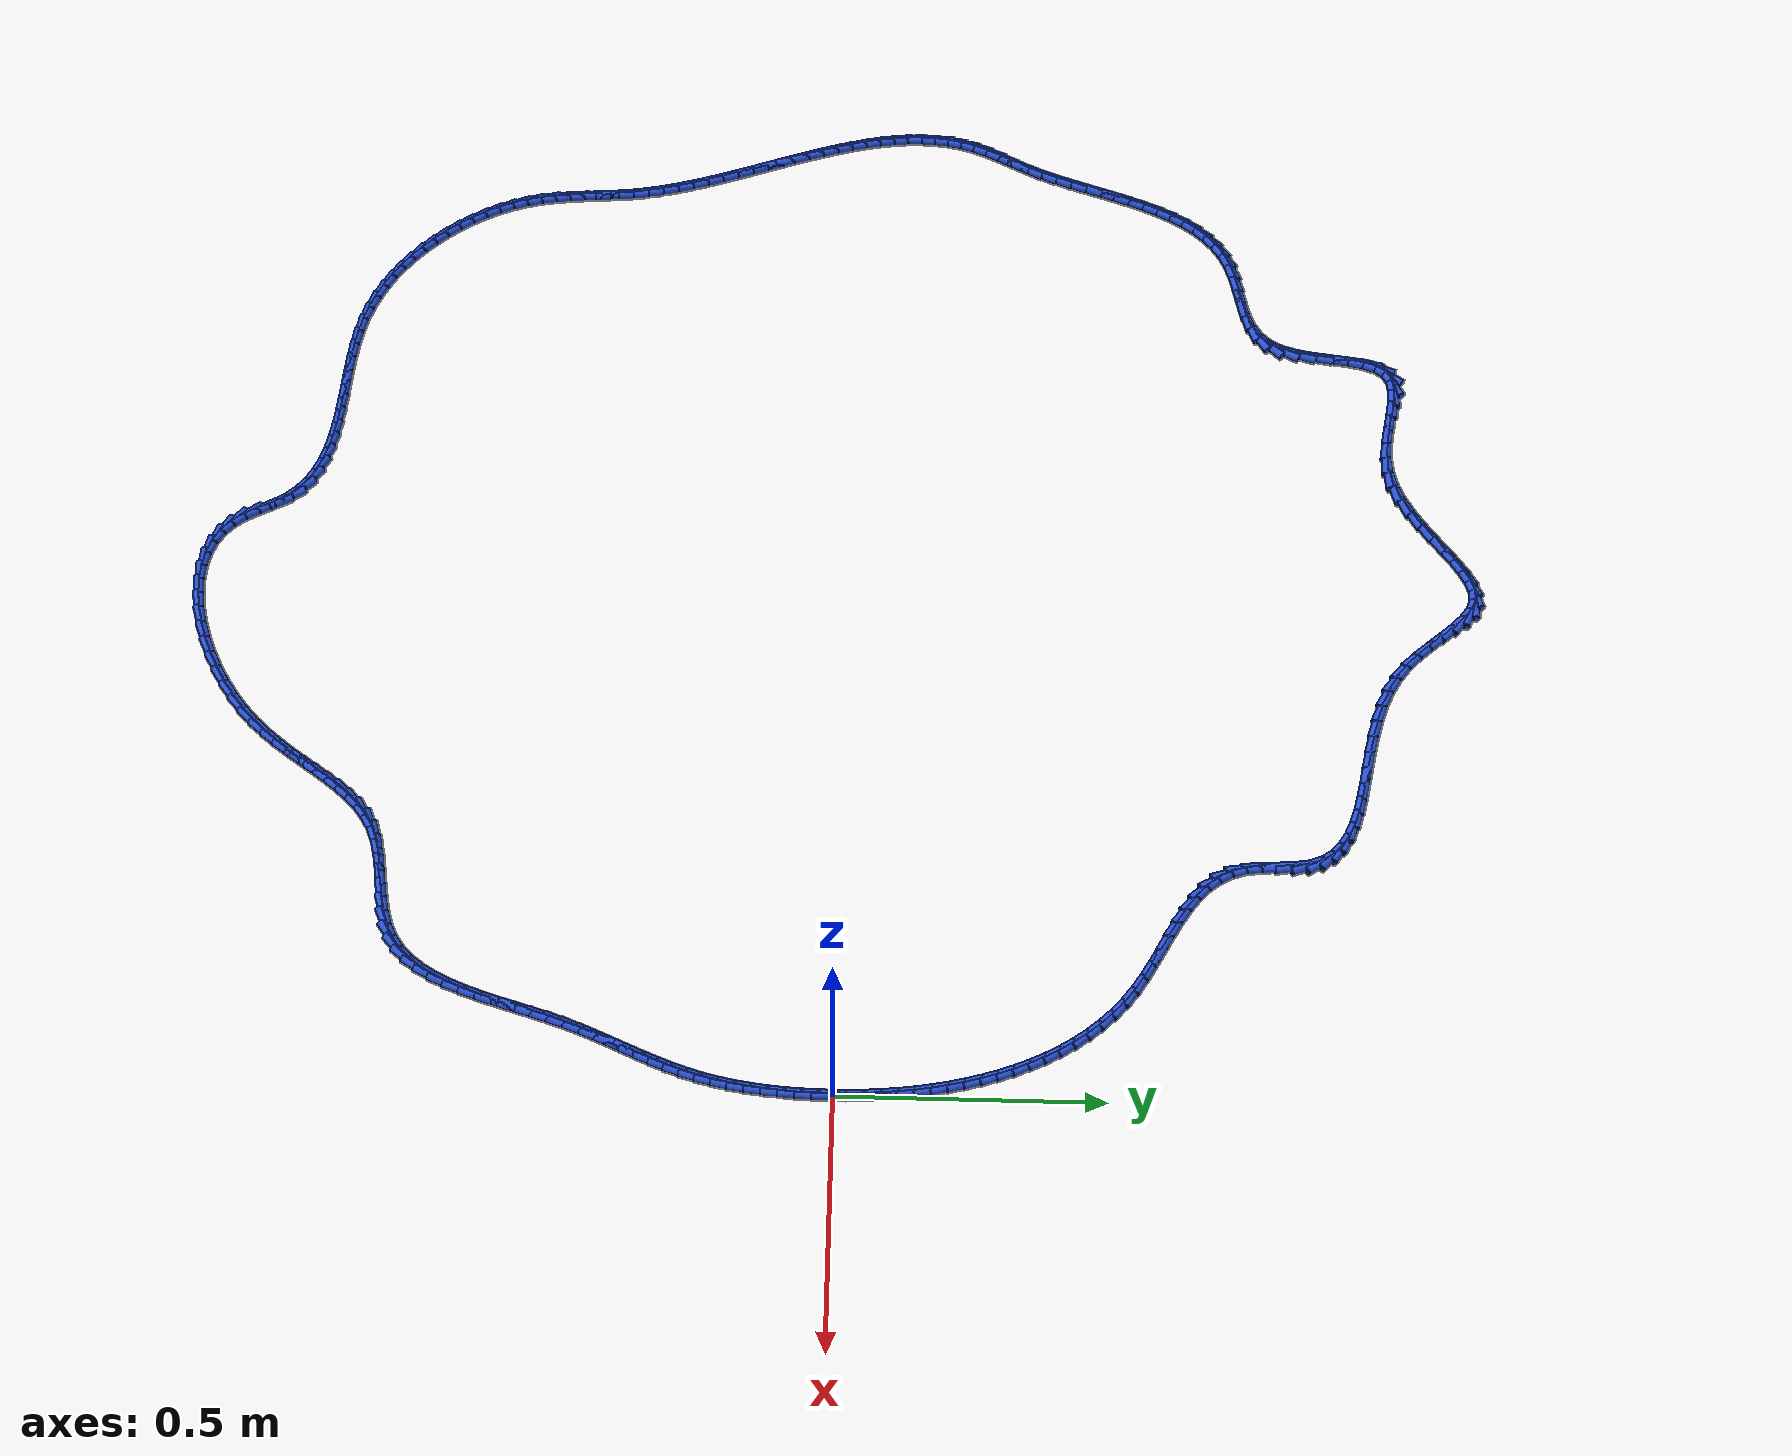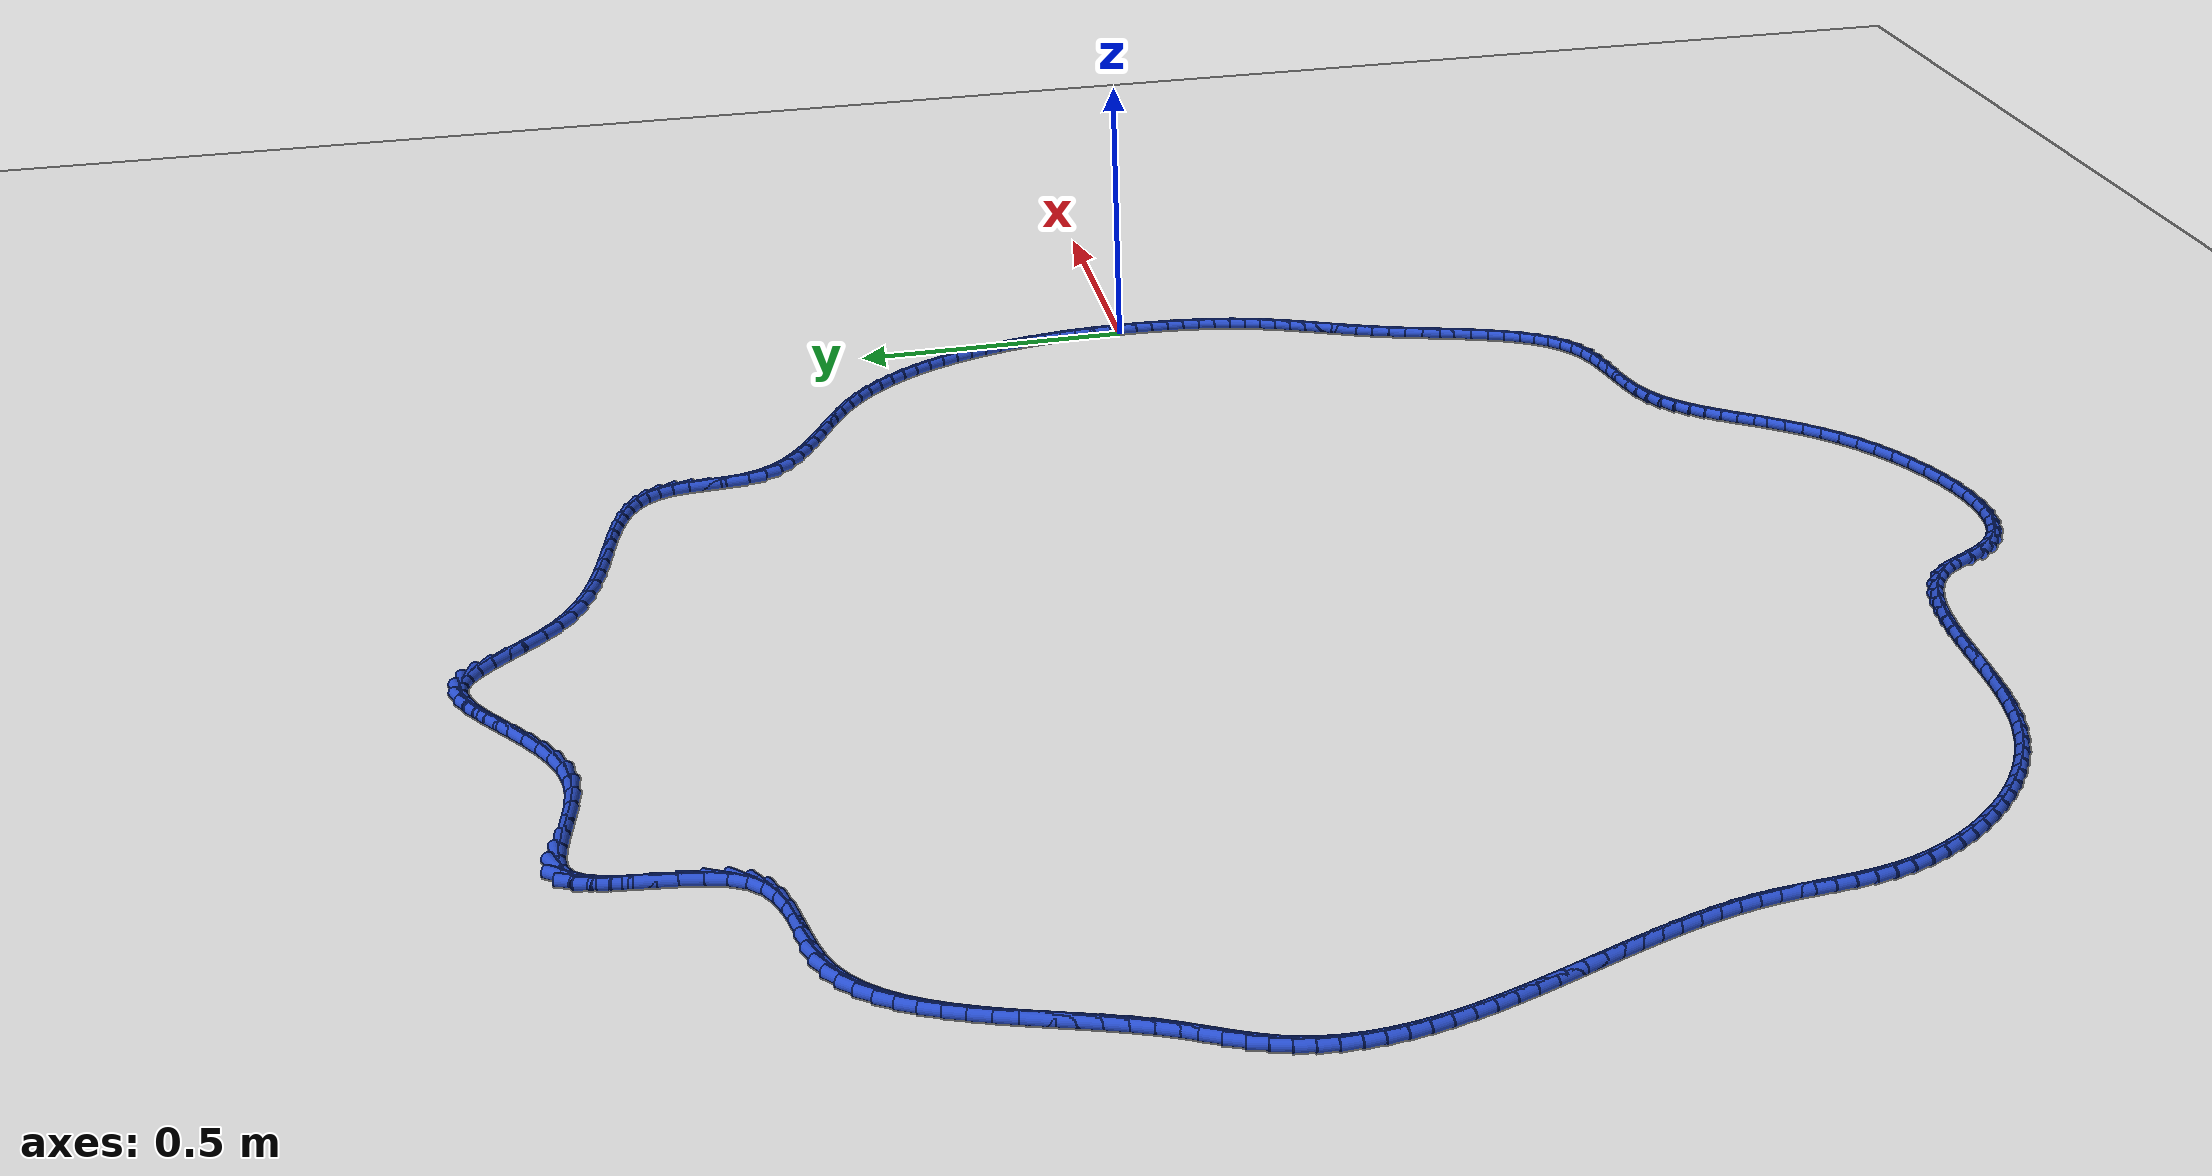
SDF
<sdf version="1.6">
 <world name="default">
  <light name="sun" type="directional">
   <pose>0 0 10 0 -0 0</pose>
   <diffuse>0.8 0.8 0.8 1</diffuse>
   <specular>0.2 0.2 0.2 1</specular>
   <attenuation>
    <range>1000</range>
    <constant>0.9</constant>
    <linear>0.01</linear>
    <quadratic>0.001</quadratic>
   </attenuation>
   <direction>-0.5 0.1 -0.9</direction>
  </light>
  <model name="ground_plane">
   <static>1</static>
   <link name="link">
    <collision name="collision">
     <geometry><plane><normal>0 0 1</normal><size>100 100</size></plane></geometry>
     <surface><friction><ode><mu>100</mu><mu2>50</mu2></ode></friction></surface>
    </collision>
    <visual name="visual">
     <cast_shadows>0</cast_shadows>
     <geometry><plane><normal>0 0 1</normal><size>100 100</size></plane></geometry>
     <material>
      <script><uri>file://media/materials/scripts/gazebo.material</uri><name>Gazebo/WhiteGlow</name></script>
     </material>
    </visual>
   </link>
  </model>
  <gravity>0 0 -9.8</gravity>
  <magnetic_field>6e-06 2.3e-05 -4.2e-05</magnetic_field>
  <atmosphere type="adiabatic"/>
  <physics name="default_physics" default="0" type="ode">
   <max_step_size>0.001</max_step_size>
   <real_time_factor>1</real_time_factor>
   <real_time_update_rate>1000</real_time_update_rate>
  </physics>
  <scene><ambient>0.4 0.4 0.4 1</ambient><background>0.7 0.7 0.7 1</background><shadows>1</shadows></scene>
  <spherical_coordinates>
   <surface_model>EARTH_WGS84</surface_model>
   <latitude_deg>0</latitude_deg>
   <longitude_deg>0</longitude_deg>
   <elevation>0</elevation>
   <heading_deg>0</heading_deg>
  </spherical_coordinates>
  <model name="line">
   <link name="link_0">
    <pose>8.673617379884035e-19 0.0 0.01 0 1.57 -1.5537155592477754</pose>
    <collision name="collision">
     <geometry><cylinder><radius>0.01</radius><length>0.08</length></cylinder></geometry>
    </collision>
    <visual name="visual">
     <material>
      <script><name>Gazebo/Blue</name><uri>file://media/materials/scripts/gazebo.material</uri></script>
     </material>
     <geometry><cylinder><radius>0.01</radius><length>0.08</length></cylinder></geometry>
    </visual>
   </link>
   <link name="link_1">
    <pose>-0.0005280388320067188 0.030911226753349168 0.01 0 1.57 -1.5272445608165166</pose>
    <collision name="collision">
     <geometry><cylinder><radius>0.01</radius><length>0.08</length></cylinder></geometry>
    </collision>
    <visual name="visual">
     <material>
      <script><name>Gazebo/Blue</name><uri>file://media/materials/scripts/gazebo.material</uri></script>
     </material>
     <geometry><cylinder><radius>0.01</radius><length>0.08</length></cylinder></geometry>
    </visual>
   </link>
   <link name="link_2">
    <pose>-0.0018693940252636548 0.06169085144220721 0.01 0 1.57 -1.4989854534255072</pose>
    <collision name="collision">
     <geometry><cylinder><radius>0.01</radius><length>0.08</length></cylinder></geometry>
    </collision>
    <visual name="visual">
     <material>
      <script><name>Gazebo/Blue</name><uri>file://media/materials/scripts/gazebo.material</uri></script>
     </material>
     <geometry><cylinder><radius>0.01</radius><length>0.08</length></cylinder></geometry>
    </visual>
   </link>
   <link name="link_3">
    <pose>-0.004073394884224138 0.09232981906603097 0.01 0 1.57 -1.468950781116024</pose>
    <collision name="collision">
     <geometry><cylinder><radius>0.01</radius><length>0.08</length></cylinder></geometry>
    </collision>
    <visual name="visual">
     <material>
      <script><name>Gazebo/Blue</name><uri>file://media/materials/scripts/gazebo.material</uri></script>
     </material>
     <geometry><cylinder><radius>0.01</radius><length>0.08</length></cylinder></geometry>
    </visual>
   </link>
   <link name="link_4">
    <pose>-0.007189370713341492 0.12281907462427716 0.01 0 1.57 -1.4371689759049169</pose>
    <collision name="collision">
     <geometry><cylinder><radius>0.01</radius><length>0.08</length></cylinder></geometry>
    </collision>
    <visual name="visual">
     <material>
      <script><name>Gazebo/Blue</name><uri>file://media/materials/scripts/gazebo.material</uri></script>
     </material>
     <geometry><cylinder><radius>0.01</radius><length>0.08</length></cylinder></geometry>
    </visual>
   </link>
   <link name="link_5">
    <pose>-0.011266650817069051 0.15314956311640274 0.01 0 1.57 -1.4036869510405978</pose>
    <collision name="collision">
     <geometry><cylinder><radius>0.01</radius><length>0.08</length></cylinder></geometry>
    </collision>
    <visual name="visual">
     <material>
      <script><name>Gazebo/Blue</name><uri>file://media/materials/scripts/gazebo.material</uri></script>
     </material>
     <geometry><cylinder><radius>0.01</radius><length>0.08</length></cylinder></geometry>
    </visual>
   </link>
   <link name="link_6">
    <pose>-0.016354564499860152 0.1833122295418645 0.01 0 1.57 -1.3685724548292852</pose>
    <collision name="collision">
     <geometry><cylinder><radius>0.01</radius><length>0.08</length></cylinder></geometry>
    </collision>
    <visual name="visual">
     <material>
      <script><name>Gazebo/Blue</name><uri>file://media/materials/scripts/gazebo.material</uri></script>
     </material>
     <geometry><cylinder><radius>0.01</radius><length>0.08</length></cylinder></geometry>
    </visual>
   </link>
   <link name="link_7">
    <pose>-0.022502441066168107 0.21329801890011915 0.01 0 1.57 -1.3319159829816518</pose>
    <collision name="collision">
     <geometry><cylinder><radius>0.01</radius><length>0.08</length></cylinder></geometry>
    </collision>
    <visual name="visual">
     <material>
      <script><name>Gazebo/Blue</name><uri>file://media/materials/scripts/gazebo.material</uri></script>
     </material>
     <geometry><cylinder><radius>0.01</radius><length>0.08</length></cylinder></geometry>
    </visual>
   </link>
   <link name="link_8">
    <pose>-0.029759609820446252 0.24309787619062362 0.01 0 1.57 -1.2937988302686025</pose>
    <collision name="collision">
     <geometry><cylinder><radius>0.01</radius><length>0.08</length></cylinder></geometry>
    </collision>
    <visual name="visual">
     <material>
      <script><name>Gazebo/Blue</name><uri>file://media/materials/scripts/gazebo.material</uri></script>
     </material>
     <geometry><cylinder><radius>0.01</radius><length>0.08</length></cylinder></geometry>
    </visual>
   </link>
   <link name="link_9">
    <pose>-0.03817584782040652 0.27270058496048133 0.01 0 1.57 -1.253406238660107</pose>
    <collision name="collision">
     <geometry><cylinder><radius>0.01</radius><length>0.08</length></cylinder></geometry>
    </collision>
    <visual name="visual">
     <material>
      <script><name>Gazebo/Blue</name><uri>file://media/materials/scripts/gazebo.material</uri></script>
     </material>
     <geometry><cylinder><radius>0.01</radius><length>0.08</length></cylinder></geometry>
    </visual>
   </link>
   <link name="link_10">
    <pose>-0.04781285189020945 0.3020373881208552 0.01 0 1.57 -1.2096071124289633</pose>
    <collision name="collision">
     <geometry><cylinder><radius>0.01</radius><length>0.08</length></cylinder></geometry>
    </collision>
    <visual name="visual">
     <material>
      <script><name>Gazebo/Blue</name><uri>file://media/materials/scripts/gazebo.material</uri></script>
     </material>
     <geometry><cylinder><radius>0.01</radius><length>0.08</length></cylinder></geometry>
    </visual>
   </link>
   <link name="link_11">
    <pose>-0.05874521572094329 0.3309772711613518 0.01 0 1.57 -1.1621118894740254</pose>
    <collision name="collision">
     <geometry><cylinder><radius>0.01</radius><length>0.08</length></cylinder></geometry>
    </collision>
    <visual name="visual">
     <material>
      <script><name>Gazebo/Blue</name><uri>file://media/materials/scripts/gazebo.material</uri></script>
     </material>
     <geometry><cylinder><radius>0.01</radius><length>0.08</length></cylinder></geometry>
    </visual>
   </link>
   <link name="link_12">
    <pose>-0.07104817655738992 0.3593861129260778 0.01 0 1.57 -1.1107030475703215</pose>
    <collision name="collision">
     <geometry><cylinder><radius>0.01</radius><length>0.08</length></cylinder></geometry>
    </collision>
    <visual name="visual">
     <material>
      <script><name>Gazebo/Blue</name><uri>file://media/materials/scripts/gazebo.material</uri></script>
     </material>
     <geometry><cylinder><radius>0.01</radius><length>0.08</length></cylinder></geometry>
    </visual>
   </link>
   <link name="link_13">
    <pose>-0.08479697164433113 0.3871297922591401 0.01 0 1.57 -1.055208674298638</pose>
    <collision name="collision">
     <geometry><cylinder><radius>0.01</radius><length>0.08</length></cylinder></geometry>
    </collision>
    <visual name="visual">
     <material>
      <script><name>Gazebo/Blue</name><uri>file://media/materials/scripts/gazebo.material</uri></script>
     </material>
     <geometry><cylinder><radius>0.01</radius><length>0.08</length></cylinder></geometry>
    </visual>
   </link>
   <link name="link_14">
    <pose>-0.10006683822654884 0.41407418800464557 0.01 0 1.57 -0.9955291498775276</pose>
    <collision name="collision">
     <geometry><cylinder><radius>0.01</radius><length>0.08</length></cylinder></geometry>
    </collision>
    <visual name="visual">
     <material>
      <script><name>Gazebo/Blue</name><uri>file://media/materials/scripts/gazebo.material</uri></script>
     </material>
     <geometry><cylinder><radius>0.01</radius><length>0.08</length></cylinder></geometry>
    </visual>
   </link>
   <link name="link_15">
    <pose>-0.11693301354882488 0.4400851790067008 0.01 0 1.57 -0.9316682070021687</pose>
    <collision name="collision">
     <geometry><cylinder><radius>0.01</radius><length>0.08</length></cylinder></geometry>
    </collision>
    <visual name="visual">
     <material>
      <script><name>Gazebo/Blue</name><uri>file://media/materials/scripts/gazebo.material</uri></script>
     </material>
     <geometry><cylinder><radius>0.01</radius><length>0.08</length></cylinder></geometry>
    </visual>
   </link>
   <link name="link_16">
    <pose>-0.1354707348559411 0.46502864410941264 0.01 0 1.57 -0.8637656660985021</pose>
    <collision name="collision">
     <geometry><cylinder><radius>0.01</radius><length>0.08</length></cylinder></geometry>
    </collision>
    <visual name="visual">
     <material>
      <script><name>Gazebo/Blue</name><uri>file://media/materials/scripts/gazebo.material</uri></script>
     </material>
     <geometry><cylinder><radius>0.01</radius><length>0.08</length></cylinder></geometry>
    </visual>
   </link>
   <link name="link_17">
    <pose>-0.1557552393926794 0.488770462156888 0.01 0 1.57 -0.7921270553024634</pose>
    <collision name="collision">
     <geometry><cylinder><radius>0.01</radius><length>0.08</length></cylinder></geometry>
    </collision>
    <visual name="visual">
     <material>
      <script><name>Gazebo/Blue</name><uri>file://media/materials/scripts/gazebo.material</uri></script>
     </material>
     <geometry><cylinder><radius>0.01</radius><length>0.08</length></cylinder></geometry>
    </visual>
   </link>
   <link name="link_18">
    <pose>-0.17786176440382157 0.5111765119932334 0.01 0 1.57 -0.7172434040278896</pose>
    <collision name="collision">
     <geometry><cylinder><radius>0.01</radius><length>0.08</length></cylinder></geometry>
    </collision>
    <visual name="visual">
     <material>
      <script><name>Gazebo/Blue</name><uri>file://media/materials/scripts/gazebo.material</uri></script>
     </material>
     <geometry><cylinder><radius>0.01</radius><length>0.08</length></cylinder></geometry>
    </visual>
   </link>
   <link name="link_19">
    <pose>-0.2018655471341496 0.5321126724625562 0.01 0 1.57 -0.6398168012515932</pose>
    <collision name="collision">
     <geometry><cylinder><radius>0.01</radius><length>0.08</length></cylinder></geometry>
    </collision>
    <visual name="visual">
     <material>
      <script><name>Gazebo/Blue</name><uri>file://media/materials/scripts/gazebo.material</uri></script>
     </material>
     <geometry><cylinder><radius>0.01</radius><length>0.08</length></cylinder></geometry>
    </visual>
   </link>
   <link name="link_20">
    <pose>-0.22784122278215033 0.551445305621514 0.01 0 1.57 -0.5680354631291024</pose>
    <collision name="collision">
     <geometry><cylinder><radius>0.01</radius><length>0.08</length></cylinder></geometry>
    </collision>
    <visual name="visual">
     <material>
      <script><name>Gazebo/Blue</name><uri>file://media/materials/scripts/gazebo.material</uri></script>
     </material>
     <geometry><cylinder><radius>0.01</radius><length>0.08</length></cylinder></geometry>
    </visual>
   </link>
   <link name="link_21">
    <pose>-0.25566332252893403 0.5692013803997522 0.01 0 1.57 -0.5190503029865586</pose>
    <collision name="collision">
     <geometry><cylinder><radius>0.01</radius><length>0.08</length></cylinder></geometry>
    </collision>
    <visual name="visual">
     <material>
      <script><name>Gazebo/Blue</name><uri>file://media/materials/scripts/gazebo.material</uri></script>
     </material>
     <geometry><cylinder><radius>0.01</radius><length>0.08</length></cylinder></geometry>
    </visual>
   </link>
   <link name="link_22">
    <pose>-0.28471762525485333 0.585800146600227 0.01 0 1.57 -0.4934573531197224</pose>
    <collision name="collision">
     <geometry><cylinder><radius>0.01</radius><length>0.08</length></cylinder></geometry>
    </collision>
    <visual name="visual">
     <material>
      <script><name>Gazebo/Blue</name><uri>file://media/materials/scripts/gazebo.material</uri></script>
     </material>
     <geometry><cylinder><radius>0.01</radius><length>0.08</length></cylinder></geometry>
    </visual>
   </link>
   <link name="link_23">
    <pose>-0.3143166843180743 0.6017196260700308 0.01 0 1.57 -0.49017274310943765</pose>
    <collision name="collision">
     <geometry><cylinder><radius>0.01</radius><length>0.08</length></cylinder></geometry>
    </collision>
    <visual name="visual">
     <material>
      <script><name>Gazebo/Blue</name><uri>file://media/materials/scripts/gazebo.material</uri></script>
     </material>
     <geometry><cylinder><radius>0.01</radius><length>0.08</length></cylinder></geometry>
    </visual>
   </link>
   <link name="link_24">
    <pose>-0.34377305307676326 0.6174378406562568 0.01 0 1.57 -0.50953794916407</pose>
    <collision name="collision">
     <geometry><cylinder><radius>0.01</radius><length>0.08</length></cylinder></geometry>
    </collision>
    <visual name="visual">
     <material>
      <script><name>Gazebo/Blue</name><uri>file://media/materials/scripts/gazebo.material</uri></script>
     </material>
     <geometry><cylinder><radius>0.01</radius><length>0.08</length></cylinder></geometry>
    </visual>
   </link>
   <link name="link_25">
    <pose>-0.372399284889086 0.6334328122059978 0.01 0 1.57 -0.5534591542436653</pose>
    <collision name="collision">
     <geometry><cylinder><radius>0.01</radius><length>0.08</length></cylinder></geometry>
    </collision>
    <visual name="visual">
     <material>
      <script><name>Gazebo/Blue</name><uri>file://media/materials/scripts/gazebo.material</uri></script>
     </material>
     <geometry><cylinder><radius>0.01</radius><length>0.08</length></cylinder></geometry>
    </visual>
   </link>
   <link name="link_26">
    <pose>-0.3995079331132088 0.6501825625663464 0.01 0 1.57 -0.6253954329557927</pose>
    <collision name="collision">
     <geometry><cylinder><radius>0.01</radius><length>0.08</length></cylinder></geometry>
    </collision>
    <visual name="visual">
     <material>
      <script><name>Gazebo/Blue</name><uri>file://media/materials/scripts/gazebo.material</uri></script>
     </material>
     <geometry><cylinder><radius>0.01</radius><length>0.08</length></cylinder></geometry>
    </visual>
   </link>
   <link name="link_27">
    <pose>-0.42441155110729767 0.6681651135843955 0.01 0 1.57 -0.7298793365535429</pose>
    <collision name="collision">
     <geometry><cylinder><radius>0.01</radius><length>0.08</length></cylinder></geometry>
    </collision>
    <visual name="visual">
     <material>
      <script><name>Gazebo/Blue</name><uri>file://media/materials/scripts/gazebo.material</uri></script>
     </material>
     <geometry><cylinder><radius>0.01</radius><length>0.08</length></cylinder></geometry>
    </visual>
   </link>
   <link name="link_28">
    <pose>-0.44642269222951875 0.687858487107238 0.01 0 1.57 -0.8707941947156681</pose>
    <collision name="collision">
     <geometry><cylinder><radius>0.01</radius><length>0.08</length></cylinder></geometry>
    </collision>
    <visual name="visual">
     <material>
      <script><name>Gazebo/Blue</name><uri>file://media/materials/scripts/gazebo.material</uri></script>
     </material>
     <geometry><cylinder><radius>0.01</radius><length>0.08</length></cylinder></geometry>
    </visual>
   </link>
   <link name="link_29">
    <pose>-0.4648539098380381 0.7097407049819666 0.01 0 1.57 -1.0474900609404227</pose>
    <collision name="collision">
     <geometry><cylinder><radius>0.01</radius><length>0.08</length></cylinder></geometry>
    </collision>
    <visual name="visual">
     <material>
      <script><name>Gazebo/Blue</name><uri>file://media/materials/scripts/gazebo.material</uri></script>
     </material>
     <geometry><cylinder><radius>0.01</radius><length>0.08</length></cylinder></geometry>
    </visual>
   </link>
   <link name="link_30">
    <pose>-0.4790177572910219 0.7342897890556743 0.01 0 1.57 -1.2495734958967832</pose>
    <collision name="collision">
     <geometry><cylinder><radius>0.01</radius><length>0.08</length></cylinder></geometry>
    </collision>
    <visual name="visual">
     <material>
      <script><name>Gazebo/Blue</name><uri>file://media/materials/scripts/gazebo.material</uri></script>
     </material>
     <geometry><cylinder><radius>0.01</radius><length>0.08</length></cylinder></geometry>
    </visual>
   </link>
   <link name="link_31">
    <pose>-0.4882316449488693 0.7619801529859537 0.01 0 1.57 -1.4248450868572338</pose>
    <collision name="collision">
     <geometry><cylinder><radius>0.01</radius><length>0.08</length></cylinder></geometry>
    </collision>
    <visual name="visual">
     <material>
      <script><name>Gazebo/Blue</name><uri>file://media/materials/scripts/gazebo.material</uri></script>
     </material>
     <geometry><cylinder><radius>0.01</radius><length>0.08</length></cylinder></geometry>
    </visual>
   </link>
   <link name="link_32">
    <pose>-0.4927330525880847 0.792602705534363 0.01 0 1.57 -1.5072319531437228</pose>
    <collision name="collision">
     <geometry><cylinder><radius>0.01</radius><length>0.08</length></cylinder></geometry>
    </collision>
    <visual name="visual">
     <material>
      <script><name>Gazebo/Blue</name><uri>file://media/materials/scripts/gazebo.material</uri></script>
     </material>
     <geometry><cylinder><radius>0.01</radius><length>0.08</length></cylinder></geometry>
    </visual>
   </link>
   <link name="link_33">
    <pose>-0.4947608712037783 0.824461538986495 0.01 0 1.57 -1.504997722143784</pose>
    <collision name="collision">
     <geometry><cylinder><radius>0.01</radius><length>0.08</length></cylinder></geometry>
    </collision>
    <visual name="visual">
     <material>
      <script><name>Gazebo/Blue</name><uri>file://media/materials/scripts/gazebo.material</uri></script>
     </material>
     <geometry><cylinder><radius>0.01</radius><length>0.08</length></cylinder></geometry>
    </visual>
   </link>
   <link name="link_34">
    <pose>-0.4968170069856924 0.8556653558343938 0.01 0 1.57 -1.4121016413993734</pose>
    <collision name="collision">
     <geometry><cylinder><radius>0.01</radius><length>0.08</length></cylinder></geometry>
    </collision>
    <visual name="visual">
     <material>
      <script><name>Gazebo/Blue</name><uri>file://media/materials/scripts/gazebo.material</uri></script>
     </material>
     <geometry><cylinder><radius>0.01</radius><length>0.08</length></cylinder></geometry>
    </visual>
   </link>
   <link name="link_35">
    <pose>-0.5014033661235693 0.8843228585701047 0.01 0 1.57 -1.2086205495595588</pose>
    <collision name="collision">
     <geometry><cylinder><radius>0.01</radius><length>0.08</length></cylinder></geometry>
    </collision>
    <visual name="visual">
     <material>
      <script><name>Gazebo/Blue</name><uri>file://media/materials/scripts/gazebo.material</uri></script>
     </material>
     <geometry><cylinder><radius>0.01</radius><length>0.08</length></cylinder></geometry>
    </visual>
   </link>
   <link name="link_36">
    <pose>-0.5106838958073353 0.9088169224619925 0.01 0 1.57 -0.9616803801868318</pose>
    <collision name="collision">
     <geometry><cylinder><radius>0.01</radius><length>0.08</length></cylinder></geometry>
    </collision>
    <visual name="visual">
     <material>
      <script><name>Gazebo/Blue</name><uri>file://media/materials/scripts/gazebo.material</uri></script>
     </material>
     <geometry><cylinder><radius>0.01</radius><length>0.08</length></cylinder></geometry>
    </visual>
   </link>
   <link name="link_37">
    <pose>-0.5248530921392358 0.9291281605893118 0.01 0 1.57 -0.7327971053964613</pose>
    <collision name="collision">
     <geometry><cylinder><radius>0.01</radius><length>0.08</length></cylinder></geometry>
    </collision>
    <visual name="visual">
     <material>
      <script><name>Gazebo/Blue</name><uri>file://media/materials/scripts/gazebo.material</uri></script>
     </material>
     <geometry><cylinder><radius>0.01</radius><length>0.08</length></cylinder></geometry>
    </visual>
   </link>
   <link name="link_38">
    <pose>-0.5433939909714063 0.9458143656067095 0.01 0 1.57 -0.5464046418848033</pose>
    <collision name="collision">
     <geometry><cylinder><radius>0.01</radius><length>0.08</length></cylinder></geometry>
    </collision>
    <visual name="visual">
     <material>
      <script><name>Gazebo/Blue</name><uri>file://media/materials/scripts/gazebo.material</uri></script>
     </material>
     <geometry><cylinder><radius>0.01</radius><length>0.08</length></cylinder></geometry>
    </visual>
   </link>
   <link name="link_39">
    <pose>-0.5657886610196561 0.9594341147683023 0.01 0 1.57 -0.4076632303359125</pose>
    <collision name="collision">
     <geometry><cylinder><radius>0.01</radius><length>0.08</length></cylinder></geometry>
    </collision>
    <visual name="visual">
     <material>
      <script><name>Gazebo/Blue</name><uri>file://media/materials/scripts/gazebo.material</uri></script>
     </material>
     <geometry><cylinder><radius>0.01</radius><length>0.08</length></cylinder></geometry>
    </visual>
   </link>
   <link name="link_40">
    <pose>-0.5915191709997935 0.9705459853282066 0.01 0 1.57 -0.3105630101603938</pose>
    <collision name="collision">
     <geometry><cylinder><radius>0.01</radius><length>0.08</length></cylinder></geometry>
    </collision>
    <visual name="visual">
     <material>
      <script><name>Gazebo/Blue</name><uri>file://media/materials/scripts/gazebo.material</uri></script>
     </material>
     <geometry><cylinder><radius>0.01</radius><length>0.08</length></cylinder></geometry>
    </visual>
   </link>
   <link name="link_41">
    <pose>-0.6200675896276278 0.9797085545405383 0.01 0 1.57 -0.2468006692864018</pose>
    <collision name="collision">
     <geometry><cylinder><radius>0.01</radius><length>0.08</length></cylinder></geometry>
    </collision>
    <visual name="visual">
     <material>
      <script><name>Gazebo/Blue</name><uri>file://media/materials/scripts/gazebo.material</uri></script>
     </material>
     <geometry><cylinder><radius>0.01</radius><length>0.08</length></cylinder></geometry>
    </visual>
   </link>
   <link name="link_42">
    <pose>-0.6509159856189676 0.9874803996594139 0.01 0 1.57 -0.20955338351126954</pose>
    <collision name="collision">
     <geometry><cylinder><radius>0.01</radius><length>0.08</length></cylinder></geometry>
    </collision>
    <visual name="visual">
     <material>
      <script><name>Gazebo/Blue</name><uri>file://media/materials/scripts/gazebo.material</uri></script>
     </material>
     <geometry><cylinder><radius>0.01</radius><length>0.08</length></cylinder></geometry>
    </visual>
   </link>
   <link name="link_43">
    <pose>-0.6835464276896216 0.9944200979389499 0.01 0 1.57 -0.19419404430804402</pose>
    <collision name="collision">
     <geometry><cylinder><radius>0.01</radius><length>0.08</length></cylinder></geometry>
    </collision>
    <visual name="visual">
     <material>
      <script><name>Gazebo/Blue</name><uri>file://media/materials/scripts/gazebo.material</uri></script>
     </material>
     <geometry><cylinder><radius>0.01</radius><length>0.08</length></cylinder></geometry>
    </visual>
   </link>
   <link name="link_44">
    <pose>-0.7174409845553988 1.0010862266332623 0.01 0 1.57 -0.19803357448685469</pose>
    <collision name="collision">
     <geometry><cylinder><radius>0.01</radius><length>0.08</length></cylinder></geometry>
    </collision>
    <visual name="visual">
     <material>
      <script><name>Gazebo/Blue</name><uri>file://media/materials/scripts/gazebo.material</uri></script>
     </material>
     <geometry><cylinder><radius>0.01</radius><length>0.08</length></cylinder></geometry>
    </visual>
   </link>
   <link name="link_45">
    <pose>-0.7520817249321085 1.008037362996468 0.01 0 1.57 -0.2199272734205374</pose>
    <collision name="collision">
     <geometry><cylinder><radius>0.01</radius><length>0.08</length></cylinder></geometry>
    </collision>
    <visual name="visual">
     <material>
      <script><name>Gazebo/Blue</name><uri>file://media/materials/scripts/gazebo.material</uri></script>
     </material>
     <geometry><cylinder><radius>0.01</radius><length>0.08</length></cylinder></geometry>
    </visual>
   </link>
   <link name="link_46">
    <pose>-0.786950717535559 1.0158320842826831 0.01 0 1.57 -0.25994709544081346</pose>
    <collision name="collision">
     <geometry><cylinder><radius>0.01</radius><length>0.08</length></cylinder></geometry>
    </collision>
    <visual name="visual">
     <material>
      <script><name>Gazebo/Blue</name><uri>file://media/materials/scripts/gazebo.material</uri></script>
     </material>
     <geometry><cylinder><radius>0.01</radius><length>0.08</length></cylinder></geometry>
    </visual>
   </link>
   <link name="link_47">
    <pose>-0.8215300310815592 1.0250289677460234 0.01 0 1.57 -0.3190936098132388</pose>
    <collision name="collision">
     <geometry><cylinder><radius>0.01</radius><length>0.08</length></cylinder></geometry>
    </collision>
    <visual name="visual">
     <material>
      <script><name>Gazebo/Blue</name><uri>file://media/materials/scripts/gazebo.material</uri></script>
     </material>
     <geometry><cylinder><radius>0.01</radius><length>0.08</length></cylinder></geometry>
    </visual>
   </link>
   <link name="link_48">
    <pose>-0.8553017342859186 1.0361865906406065 0.01 0 1.57 -0.3989254796417109</pose>
    <collision name="collision">
     <geometry><cylinder><radius>0.01</radius><length>0.08</length></cylinder></geometry>
    </collision>
    <visual name="visual">
     <material>
      <script><name>Gazebo/Blue</name><uri>file://media/materials/scripts/gazebo.material</uri></script>
     </material>
     <geometry><cylinder><radius>0.01</radius><length>0.08</length></cylinder></geometry>
    </visual>
   </link>
   <link name="link_49">
    <pose>-0.8877478958644448 1.0498635302205472 0.01 0 1.57 -0.5009183164603683</pose>
    <collision name="collision">
     <geometry><cylinder><radius>0.01</radius><length>0.08</length></cylinder></geometry>
    </collision>
    <visual name="visual">
     <material>
      <script><name>Gazebo/Blue</name><uri>file://media/materials/scripts/gazebo.material</uri></script>
     </material>
     <geometry><cylinder><radius>0.01</radius><length>0.08</length></cylinder></geometry>
    </visual>
   </link>
   <link name="link_50">
    <pose>-0.9183505845329478 1.066618363739963 0.01 0 1.57 -0.6248203007541467</pose>
    <collision name="collision">
     <geometry><cylinder><radius>0.01</radius><length>0.08</length></cylinder></geometry>
    </collision>
    <visual name="visual">
     <material>
      <script><name>Gazebo/Blue</name><uri>file://media/materials/scripts/gazebo.material</uri></script>
     </material>
     <geometry><cylinder><radius>0.01</radius><length>0.08</length></cylinder></geometry>
    </visual>
   </link>
   <link name="link_51">
    <pose>-0.9465997767773 1.0869919986101606 0.01 0 1.57 -0.7422120311775847</pose>
    <collision name="collision">
     <geometry><cylinder><radius>0.01</radius><length>0.08</length></cylinder></geometry>
    </collision>
    <visual name="visual">
     <material>
      <script><name>Gazebo/Blue</name><uri>file://media/materials/scripts/gazebo.material</uri></script>
     </material>
     <geometry><cylinder><radius>0.01</radius><length>0.08</length></cylinder></geometry>
    </visual>
   </link>
   <link name="link_52">
    <pose>-0.9723823123274653 1.110638554806441 0.01 0 1.57 -0.8162339817513774</pose>
    <collision name="collision">
     <geometry><cylinder><radius>0.01</radius><length>0.08</length></cylinder></geometry>
    </collision>
    <visual name="visual">
     <material>
      <script><name>Gazebo/Blue</name><uri>file://media/materials/scripts/gazebo.material</uri></script>
     </material>
     <geometry><cylinder><radius>0.01</radius><length>0.08</length></cylinder></geometry>
    </visual>
   </link>
   <link name="link_53">
    <pose>-0.9961592680435642 1.1359290244763327 0.01 0 1.57 -0.8469782176786365</pose>
    <collision name="collision">
     <geometry><cylinder><radius>0.01</radius><length>0.08</length></cylinder></geometry>
    </collision>
    <visual name="visual">
     <material>
      <script><name>Gazebo/Blue</name><uri>file://media/materials/scripts/gazebo.material</uri></script>
     </material>
     <geometry><cylinder><radius>0.01</radius><length>0.08</length></cylinder></geometry>
    </visual>
   </link>
   <link name="link_54">
    <pose>-1.0184366282421053 1.16113405445018 0.01 0 1.57 -0.8325157192100264</pose>
    <collision name="collision">
     <geometry><cylinder><radius>0.01</radius><length>0.08</length></cylinder></geometry>
    </collision>
    <visual name="visual">
     <material>
      <script><name>Gazebo/Blue</name><uri>file://media/materials/scripts/gazebo.material</uri></script>
     </material>
     <geometry><cylinder><radius>0.01</radius><length>0.08</length></cylinder></geometry>
    </visual>
   </link>
   <link name="link_55">
    <pose>-1.0397203772395969 1.1845242915583254 0.01 0 1.57 -0.762026944508734</pose>
    <collision name="collision">
     <geometry><cylinder><radius>0.01</radius><length>0.08</length></cylinder></geometry>
    </collision>
    <visual name="visual">
     <material>
      <script><name>Gazebo/Blue</name><uri>file://media/materials/scripts/gazebo.material</uri></script>
     </material>
     <geometry><cylinder><radius>0.01</radius><length>0.08</length></cylinder></geometry>
    </visual>
   </link>
   <link name="link_56">
    <pose>-1.0605164993525467 1.2043703826311127 0.01 0 1.57 -0.6108051571364453</pose>
    <collision name="collision">
     <geometry><cylinder><radius>0.01</radius><length>0.08</length></cylinder></geometry>
    </collision>
    <visual name="visual">
     <material>
      <script><name>Gazebo/Blue</name><uri>file://media/materials/scripts/gazebo.material</uri></script>
     </material>
     <geometry><cylinder><radius>0.01</radius><length>0.08</length></cylinder></geometry>
    </visual>
   </link>
   <link name="link_57">
    <pose>-1.0813309788974639 1.2189429744988864 0.01 0 1.57 -0.3414604962938436</pose>
    <collision name="collision">
     <geometry><cylinder><radius>0.01</radius><length>0.08</length></cylinder></geometry>
    </collision>
    <visual name="visual">
     <material>
      <script><name>Gazebo/Blue</name><uri>file://media/materials/scripts/gazebo.material</uri></script>
     </material>
     <geometry><cylinder><radius>0.01</radius><length>0.08</length></cylinder></geometry>
    </visual>
   </link>
   <link name="link_58">
    <pose>-1.1026678229862463 1.226525682986013 0.01 0 1.57 0.003880813868161539</pose>
    <collision name="collision">
     <geometry><cylinder><radius>0.01</radius><length>0.08</length></cylinder></geometry>
    </collision>
    <visual name="visual">
     <material>
      <script><name>Gazebo/Blue</name><uri>file://media/materials/scripts/gazebo.material</uri></script>
     </material>
     <geometry><cylinder><radius>0.01</radius><length>0.08</length></cylinder></geometry>
    </visual>
   </link>
   <link name="link_59">
    <pose>-1.1248728828810233 1.2264395088490148 0.01 0 1.57 0.27999174864736504</pose>
    <collision name="collision">
     <geometry><cylinder><radius>0.01</radius><length>0.08</length></cylinder></geometry>
    </collision>
    <visual name="visual">
     <material>
      <script><name>Gazebo/Blue</name><uri>file://media/materials/scripts/gazebo.material</uri></script>
     </material>
     <geometry><cylinder><radius>0.01</radius><length>0.08</length></cylinder></geometry>
    </visual>
   </link>
   <link name="link_60">
    <pose>-1.148020952443739 1.219783388109623 0.01 0 1.57 0.45975655175047264</pose>
    <collision name="collision">
     <geometry><cylinder><radius>0.01</radius><length>0.08</length></cylinder></geometry>
    </collision>
    <visual name="visual">
     <material>
      <script><name>Gazebo/Blue</name><uri>file://media/materials/scripts/gazebo.material</uri></script>
     </material>
     <geometry><cylinder><radius>0.01</radius><length>0.08</length></cylinder></geometry>
    </visual>
   </link>
   <link name="link_61">
    <pose>-1.1721601925134988 1.2078309496424022 0.01 0 1.57 0.5653824780719057</pose>
    <collision name="collision">
     <geometry><cylinder><radius>0.01</radius><length>0.08</length></cylinder></geometry>
    </collision>
    <visual name="visual">
     <material>
      <script><name>Gazebo/Blue</name><uri>file://media/materials/scripts/gazebo.material</uri></script>
     </material>
     <geometry><cylinder><radius>0.01</radius><length>0.08</length></cylinder></geometry>
    </visual>
   </link>
   <link name="link_62">
    <pose>-1.1973387639294095 1.1918558223219198 0.01 0 1.57 0.6193088644832283</pose>
    <collision name="collision">
     <geometry><cylinder><radius>0.01</radius><length>0.08</length></cylinder></geometry>
    </collision>
    <visual name="visual">
     <material>
      <script><name>Gazebo/Blue</name><uri>file://media/materials/scripts/gazebo.material</uri></script>
     </material>
     <geometry><cylinder><radius>0.01</radius><length>0.08</length></cylinder></geometry>
    </visual>
   </link>
   <link name="link_63">
    <pose>-1.223604827530578 1.1731316350227405 0.01 0 1.57 0.635236731874771</pose>
    <collision name="collision">
     <geometry><cylinder><radius>0.01</radius><length>0.08</length></cylinder></geometry>
    </collision>
    <visual name="visual">
     <material>
      <script><name>Gazebo/Blue</name><uri>file://media/materials/scripts/gazebo.material</uri></script>
     </material>
     <geometry><cylinder><radius>0.01</radius><length>0.08</length></cylinder></geometry>
    </visual>
   </link>
   <link name="link_64">
    <pose>-1.2510065441561096 1.152932016619431 0.01 0 1.57 0.6198598608830022</pose>
    <collision name="collision">
     <geometry><cylinder><radius>0.01</radius><length>0.08</length></cylinder></geometry>
    </collision>
    <visual name="visual">
     <material>
      <script><name>Gazebo/Blue</name><uri>file://media/materials/scripts/gazebo.material</uri></script>
     </material>
     <geometry><cylinder><radius>0.01</radius><length>0.08</length></cylinder></geometry>
    </visual>
   </link>
   <link name="link_65">
    <pose>-1.279592074645112 1.132530595986558 0.01 0 1.57 0.5751533651573076</pose>
    <collision name="collision">
     <geometry><cylinder><radius>0.01</radius><length>0.08</length></cylinder></geometry>
    </collision>
    <visual name="visual">
     <material>
      <script><name>Gazebo/Blue</name><uri>file://media/materials/scripts/gazebo.material</uri></script>
     </material>
     <geometry><cylinder><radius>0.01</radius><length>0.08</length></cylinder></geometry>
    </visual>
   </link>
   <link name="link_66">
    <pose>-1.3094095798366912 1.1132010019986862 0.01 0 1.57 0.4998865643165475</pose>
    <collision name="collision">
     <geometry><cylinder><radius>0.01</radius><length>0.08</length></cylinder></geometry>
    </collision>
    <visual name="visual">
     <material>
      <script><name>Gazebo/Blue</name><uri>file://media/materials/scripts/gazebo.material</uri></script>
     </material>
     <geometry><cylinder><radius>0.01</radius><length>0.08</length></cylinder></geometry>
    </visual>
   </link>
   <link name="link_67">
    <pose>-1.3405072205699533 1.0962168635303824 0.01 0 1.57 0.39095499769523057</pose>
    <collision name="collision">
     <geometry><cylinder><radius>0.01</radius><length>0.08</length></cylinder></geometry>
    </collision>
    <visual name="visual">
     <material>
      <script><name>Gazebo/Blue</name><uri>file://media/materials/scripts/gazebo.material</uri></script>
     </material>
     <geometry><cylinder><radius>0.01</radius><length>0.08</length></cylinder></geometry>
    </visual>
   </link>
   <link name="link_68">
    <pose>-1.3729331576840047 1.0828518094562123 0.01 0 1.57 0.24558395068451289</pose>
    <collision name="collision">
     <geometry><cylinder><radius>0.01</radius><length>0.08</length></cylinder></geometry>
    </collision>
    <visual name="visual">
     <material>
      <script><name>Gazebo/Blue</name><uri>file://media/materials/scripts/gazebo.material</uri></script>
     </material>
     <geometry><cylinder><radius>0.01</radius><length>0.08</length></cylinder></geometry>
    </visual>
   </link>
   <link name="link_69">
    <pose>-1.4067355520179523 1.0743794686507426 0.01 0 1.57 0.07316014803526646</pose>
    <collision name="collision">
     <geometry><cylinder><radius>0.01</radius><length>0.08</length></cylinder></geometry>
    </collision>
    <visual name="visual">
     <material>
      <script><name>Gazebo/Blue</name><uri>file://media/materials/scripts/gazebo.material</uri></script>
     </material>
     <geometry><cylinder><radius>0.01</radius><length>0.08</length></cylinder></geometry>
    </visual>
   </link>
   <link name="link_70">
    <pose>-1.4418786087152187 1.0718038004380324 0.01 0 1.57 -0.06365221837223159</pose>
    <collision name="collision">
     <geometry><cylinder><radius>0.01</radius><length>0.08</length></cylinder></geometry>
    </collision>
    <visual name="visual">
     <material>
      <script><name>Gazebo/Blue</name><uri>file://media/materials/scripts/gazebo.material</uri></script>
     </material>
     <geometry><cylinder><radius>0.01</radius><length>0.08</length></cylinder></geometry>
    </visual>
   </link>
   <link name="link_71">
    <pose>-1.4776906883930805 1.074086402320701 0.01 0 1.57 -0.14447199310807457</pose>
    <collision name="collision">
     <geometry><cylinder><radius>0.01</radius><length>0.08</length></cylinder></geometry>
    </collision>
    <visual name="visual">
     <material>
      <script><name>Gazebo/Blue</name><uri>file://media/materials/scripts/gazebo.material</uri></script>
     </material>
     <geometry><cylinder><radius>0.01</radius><length>0.08</length></cylinder></geometry>
    </visual>
   </link>
   <link name="link_72">
    <pose>-1.5132090411086754 1.0792538113118892 0.01 0 1.57 -0.1754634651041353</pose>
    <collision name="collision">
     <geometry><cylinder><radius>0.01</radius><length>0.08</length></cylinder></geometry>
    </collision>
    <visual name="visual">
     <material>
      <script><name>Gazebo/Blue</name><uri>file://media/materials/scripts/gazebo.material</uri></script>
     </material>
     <geometry><cylinder><radius>0.01</radius><length>0.08</length></cylinder></geometry>
    </visual>
   </link>
   <link name="link_73">
    <pose>-1.5474694073101893 1.0853277154914547 0.01 0 1.57 -0.15487886077908944</pose>
    <collision name="collision">
     <geometry><cylinder><radius>0.01</radius><length>0.08</length></cylinder></geometry>
    </collision>
    <visual name="visual">
     <material>
      <script><name>Gazebo/Blue</name><uri>file://media/materials/scripts/gazebo.material</uri></script>
     </material>
     <geometry><cylinder><radius>0.01</radius><length>0.08</length></cylinder></geometry>
    </visual>
   </link>
   <link name="link_74">
    <pose>-1.5795075274458088 1.0903298029392539 0.01 0 1.57 -0.06755215624151038</pose>
    <collision name="collision">
     <geometry><cylinder><radius>0.01</radius><length>0.08</length></cylinder></geometry>
    </collision>
    <visual name="visual">
     <material>
      <script><name>Gazebo/Blue</name><uri>file://media/materials/scripts/gazebo.material</uri></script>
     </material>
     <geometry><cylinder><radius>0.01</radius><length>0.08</length></cylinder></geometry>
    </visual>
   </link>
   <link name="link_75">
    <pose>-1.6083591419637193 1.0922817617351437 0.01 0 1.57 0.12391153391176991</pose>
    <collision name="collision">
     <geometry><cylinder><radius>0.01</radius><length>0.08</length></cylinder></geometry>
    </collision>
    <visual name="visual">
     <material>
      <script><name>Gazebo/Blue</name><uri>file://media/materials/scripts/gazebo.material</uri></script>
     </material>
     <geometry><cylinder><radius>0.01</radius><length>0.08</length></cylinder></geometry>
    </visual>
   </link>
   <link name="link_76">
    <pose>-1.6330599913121073 1.0892052799589815 0.01 0 1.57 0.47543561808769347</pose>
    <collision name="collision">
     <geometry><cylinder><radius>0.01</radius><length>0.08</length></cylinder></geometry>
    </collision>
    <visual name="visual">
     <material>
      <script><name>Gazebo/Blue</name><uri>file://media/materials/scripts/gazebo.material</uri></script>
     </material>
     <geometry><cylinder><radius>0.01</radius><length>0.08</length></cylinder></geometry>
    </visual>
   </link>
   <link name="link_77">
    <pose>-1.65264581593916 1.0791220456906245 0.01 0 1.57 0.9252139726959562</pose>
    <collision name="collision">
     <geometry><cylinder><radius>0.01</radius><length>0.08</length></cylinder></geometry>
    </collision>
    <visual name="visual">
     <material>
      <script><name>Gazebo/Blue</name><uri>file://media/materials/scripts/gazebo.material</uri></script>
     </material>
     <geometry><cylinder><radius>0.01</radius><length>0.08</length></cylinder></geometry>
    </visual>
   </link>
   <link name="link_78">
    <pose>-1.6665434936616992 1.06067193226871 0.01 0 1.57 1.2213101138235727</pose>
    <collision name="collision">
     <geometry><cylinder><radius>0.01</radius><length>0.08</length></cylinder></geometry>
    </collision>
    <visual name="visual">
     <material>
      <script><name>Gazebo/Blue</name><uri>file://media/materials/scripts/gazebo.material</uri></script>
     </material>
     <geometry><cylinder><radius>0.01</radius><length>0.08</length></cylinder></geometry>
    </visual>
   </link>
   <link name="link_79">
    <pose>-1.6758503583821003 1.0351349374749295 0.01 0 1.57 1.3692804238048197</pose>
    <collision name="collision">
     <geometry><cylinder><radius>0.01</radius><length>0.08</length></cylinder></geometry>
    </collision>
    <visual name="visual">
     <material>
      <script><name>Gazebo/Blue</name><uri>file://media/materials/scripts/gazebo.material</uri></script>
     </material>
     <geometry><cylinder><radius>0.01</radius><length>0.08</length></cylinder></geometry>
    </visual>
   </link>
   <link name="link_80">
    <pose>-1.6821096026532059 1.0044957303070698 0.01 0 1.57 1.4308614960038961</pose>
    <collision name="collision">
     <geometry><cylinder><radius>0.01</radius><length>0.08</length></cylinder></geometry>
    </collision>
    <visual name="visual">
     <material>
      <script><name>Gazebo/Blue</name><uri>file://media/materials/scripts/gazebo.material</uri></script>
     </material>
     <geometry><cylinder><radius>0.01</radius><length>0.08</length></cylinder></geometry>
    </visual>
   </link>
   <link name="link_81">
    <pose>-1.6868644233735355 0.9707389866311821 0.01 0 1.57 1.4342579929798316</pose>
    <collision name="collision">
     <geometry><cylinder><radius>0.01</radius><length>0.08</length></cylinder></geometry>
    </collision>
    <visual name="visual">
     <material>
      <script><name>Gazebo/Blue</name><uri>file://media/materials/scripts/gazebo.material</uri></script>
     </material>
     <geometry><cylinder><radius>0.01</radius><length>0.08</length></cylinder></geometry>
    </visual>
   </link>
   <link name="link_82">
    <pose>-1.6916580174416092 0.9358493823133178 0.01 0 1.57 1.3856334618695747</pose>
    <collision name="collision">
     <geometry><cylinder><radius>0.01</radius><length>0.08</length></cylinder></geometry>
    </collision>
    <visual name="visual">
     <material>
      <script><name>Gazebo/Blue</name><uri>file://media/materials/scripts/gazebo.material</uri></script>
     </material>
     <geometry><cylinder><radius>0.01</radius><length>0.08</length></cylinder></geometry>
    </visual>
   </link>
   <link name="link_83">
    <pose>-1.6980335817559487 0.9018115932195282 0.01 0 1.57 1.2752180929821504</pose>
    <collision name="collision">
     <geometry><cylinder><radius>0.01</radius><length>0.08</length></cylinder></geometry>
    </collision>
    <visual name="visual">
     <material>
      <script><name>Gazebo/Blue</name><uri>file://media/materials/scripts/gazebo.material</uri></script>
     </material>
     <geometry><cylinder><radius>0.01</radius><length>0.08</length></cylinder></geometry>
    </visual>
   </link>
   <link name="link_84">
    <pose>-1.707534313215073 0.8706102952158641 0.01 0 1.57 1.077901438491657</pose>
    <collision name="collision">
     <geometry><cylinder><radius>0.01</radius><length>0.08</length></cylinder></geometry>
    </collision>
    <visual name="visual">
     <material>
      <script><name>Gazebo/Blue</name><uri>file://media/materials/scripts/gazebo.material</uri></script>
     </material>
     <geometry><cylinder><radius>0.01</radius><length>0.08</length></cylinder></geometry>
    </visual>
   </link>
   <link name="link_85">
    <pose>-1.721703408717503 0.8442301641683763 0.01 0 1.57 0.786217073422898</pose>
    <collision name="collision">
     <geometry><cylinder><radius>0.01</radius><length>0.08</length></cylinder></geometry>
    </collision>
    <visual name="visual">
     <material>
      <script><name>Gazebo/Blue</name><uri>file://media/materials/scripts/gazebo.material</uri></script>
     </material>
     <geometry><cylinder><radius>0.01</radius><length>0.08</length></cylinder></geometry>
    </visual>
   </link>
   <link name="link_86">
    <pose>-1.741703747003512 0.8241970420729791 0.01 0 1.57 0.5228910142721227</pose>
    <collision name="collision">
     <geometry><cylinder><radius>0.01</radius><length>0.08</length></cylinder></geometry>
    </collision>
    <visual name="visual">
     <material>
      <script><name>Gazebo/Blue</name><uri>file://media/materials/scripts/gazebo.material</uri></script>
     </material>
     <geometry><cylinder><radius>0.01</radius><length>0.08</length></cylinder></geometry>
    </visual>
   </link>
   <link name="link_87">
    <pose>-1.7667914197651091 0.8097363325638887 0.01 0 1.57 0.345610851170592</pose>
    <collision name="collision">
     <geometry><cylinder><radius>0.01</radius><length>0.08</length></cylinder></geometry>
    </collision>
    <visual name="visual">
     <material>
      <script><name>Gazebo/Blue</name><uri>file://media/materials/scripts/gazebo.material</uri></script>
     </material>
     <geometry><cylinder><radius>0.01</radius><length>0.08</length></cylinder></geometry>
    </visual>
   </link>
   <link name="link_88">
    <pose>-1.795626199535456 0.7993540115499851 0.01 0 1.57 0.24461222767806393</pose>
    <collision name="collision">
     <geometry><cylinder><radius>0.01</radius><length>0.08</length></cylinder></geometry>
    </collision>
    <visual name="visual">
     <material>
      <script><name>Gazebo/Blue</name><uri>file://media/materials/scripts/gazebo.material</uri></script>
     </material>
     <geometry><cylinder><radius>0.01</radius><length>0.08</length></cylinder></geometry>
    </visual>
   </link>
   <link name="link_89">
    <pose>-1.8268676557121408 0.7915558098677569 0.01 0 1.57 0.20473021946640144</pose>
    <collision name="collision">
     <geometry><cylinder><radius>0.01</radius><length>0.08</length></cylinder></geometry>
    </collision>
    <visual name="visual">
     <material>
      <script><name>Gazebo/Blue</name><uri>file://media/materials/scripts/gazebo.material</uri></script>
     </material>
     <geometry><cylinder><radius>0.01</radius><length>0.08</length></cylinder></geometry>
    </visual>
   </link>
   <link name="link_90">
    <pose>-1.8591753576927514 0.7848474583536921 0.01 0 1.57 0.2184967306821728</pose>
    <collision name="collision">
     <geometry><cylinder><radius>0.01</radius><length>0.08</length></cylinder></geometry>
    </collision>
    <visual name="visual">
     <material>
      <script><name>Gazebo/Blue</name><uri>file://media/materials/scripts/gazebo.material</uri></script>
     </material>
     <geometry><cylinder><radius>0.01</radius><length>0.08</length></cylinder></geometry>
    </visual>
   </link>
   <link name="link_91">
    <pose>-1.8912088748748765 0.7777346878442788 0.01 0 1.57 0.2880086257925667</pose>
    <collision name="collision">
     <geometry><cylinder><radius>0.01</radius><length>0.08</length></cylinder></geometry>
    </collision>
    <visual name="visual">
     <material>
      <script><name>Gazebo/Blue</name><uri>file://media/materials/scripts/gazebo.material</uri></script>
     </material>
     <geometry><cylinder><radius>0.01</radius><length>0.08</length></cylinder></geometry>
    </visual>
   </link>
   <link name="link_92">
    <pose>-1.921627776656104 0.7687232291760054 0.01 0 1.57 0.4163069476465975</pose>
    <collision name="collision">
     <geometry><cylinder><radius>0.01</radius><length>0.08</length></cylinder></geometry>
    </collision>
    <visual name="visual">
     <material>
      <script><name>Gazebo/Blue</name><uri>file://media/materials/scripts/gazebo.material</uri></script>
     </material>
     <geometry><cylinder><radius>0.01</radius><length>0.08</length></cylinder></geometry>
    </visual>
   </link>
   <link name="link_93">
    <pose>-1.9492593412892008 0.7565059253407277 0.01 0 1.57 0.5617841234947448</pose>
    <collision name="collision">
     <geometry><cylinder><radius>0.01</radius><length>0.08</length></cylinder></geometry>
    </collision>
    <visual name="visual">
     <material>
      <script><name>Gazebo/Blue</name><uri>file://media/materials/scripts/gazebo.material</uri></script>
     </material>
     <geometry><cylinder><radius>0.01</radius><length>0.08</length></cylinder></geometry>
    </visual>
   </link>
   <link name="link_94">
    <pose>-1.9739798021772224 0.7409459347489292 0.01 0 1.57 0.6995108405823739</pose>
    <collision name="collision">
     <geometry><cylinder><radius>0.01</radius><length>0.08</length></cylinder></geometry>
    </collision>
    <visual name="visual">
     <material>
      <script><name>Gazebo/Blue</name><uri>file://media/materials/scripts/gazebo.material</uri></script>
     </material>
     <geometry><cylinder><radius>0.01</radius><length>0.08</length></cylinder></geometry>
    </visual>
   </link>
   <link name="link_95">
    <pose>-1.9960701263088925 0.7223579755899959 0.01 0 1.57 0.823346452514652</pose>
    <collision name="collision">
     <geometry><cylinder><radius>0.01</radius><length>0.08</length></cylinder></geometry>
    </collision>
    <visual name="visual">
     <material>
      <script><name>Gazebo/Blue</name><uri>file://media/materials/scripts/gazebo.material</uri></script>
     </material>
     <geometry><cylinder><radius>0.01</radius><length>0.08</length></cylinder></geometry>
    </visual>
   </link>
   <link name="link_96">
    <pose>-2.015812142518921 0.7010577276117222 0.01 0 1.57 0.9299229911424787</pose>
    <collision name="collision">
     <geometry><cylinder><radius>0.01</radius><length>0.08</length></cylinder></geometry>
    </collision>
    <visual name="visual">
     <material>
      <script><name>Gazebo/Blue</name><uri>file://media/materials/scripts/gazebo.material</uri></script>
     </material>
     <geometry><cylinder><radius>0.01</radius><length>0.08</length></cylinder></geometry>
    </visual>
   </link>
   <link name="link_97">
    <pose>-2.0334876796420183 0.677360870561904 0.01 0 1.57 1.0183641731694952</pose>
    <collision name="collision">
     <geometry><cylinder><radius>0.01</radius><length>0.08</length></cylinder></geometry>
    </collision>
    <visual name="visual">
     <material>
      <script><name>Gazebo/Blue</name><uri>file://media/materials/scripts/gazebo.material</uri></script>
     </material>
     <geometry><cylinder><radius>0.01</radius><length>0.08</length></cylinder></geometry>
    </visual>
   </link>
   <link name="link_98">
    <pose>-2.049378566512891 0.6515830841883351 0.01 0 1.57 1.0894016029265934</pose>
    <collision name="collision">
     <geometry><cylinder><radius>0.01</radius><length>0.08</length></cylinder></geometry>
    </collision>
    <visual name="visual">
     <material>
      <script><name>Gazebo/Blue</name><uri>file://media/materials/scripts/gazebo.material</uri></script>
     </material>
     <geometry><cylinder><radius>0.01</radius><length>0.08</length></cylinder></geometry>
    </visual>
   </link>
   <link name="link_99">
    <pose>-2.0637666319662515 0.6240400482388109 0.01 0 1.57 1.1444943073441882</pose>
    <collision name="collision">
     <geometry><cylinder><radius>0.01</radius><length>0.08</length></cylinder></geometry>
    </collision>
    <visual name="visual">
     <material>
      <script><name>Gazebo/Blue</name><uri>file://media/materials/scripts/gazebo.material</uri></script>
     </material>
     <geometry><cylinder><radius>0.01</radius><length>0.08</length></cylinder></geometry>
    </visual>
   </link>
   <link name="link_100">
    <pose>-2.076933704836808 0.5950474424611257 0.01 0 1.57 1.1852265255010952</pose>
    <collision name="collision">
     <geometry><cylinder><radius>0.01</radius><length>0.08</length></cylinder></geometry>
    </collision>
    <visual name="visual">
     <material>
      <script><name>Gazebo/Blue</name><uri>file://media/materials/scripts/gazebo.material</uri></script>
     </material>
     <geometry><cylinder><radius>0.01</radius><length>0.08</length></cylinder></geometry>
    </visual>
   </link>
   <link name="link_101">
    <pose>-2.0891616139592695 0.5649209466030753 0.01 0 1.57 1.212980506196031</pose>
    <collision name="collision">
     <geometry><cylinder><radius>0.01</radius><length>0.08</length></cylinder></geometry>
    </collision>
    <visual name="visual">
     <material>
      <script><name>Gazebo/Blue</name><uri>file://media/materials/scripts/gazebo.material</uri></script>
     </material>
     <geometry><cylinder><radius>0.01</radius><length>0.08</length></cylinder></geometry>
    </visual>
   </link>
   <link name="link_102">
    <pose>-2.100732188168347 0.533976240412454 0.01 0 1.57 1.2287905092218045</pose>
    <collision name="collision">
     <geometry><cylinder><radius>0.01</radius><length>0.08</length></cylinder></geometry>
    </collision>
    <visual name="visual">
     <material>
      <script><name>Gazebo/Blue</name><uri>file://media/materials/scripts/gazebo.material</uri></script>
     </material>
     <geometry><cylinder><radius>0.01</radius><length>0.08</length></cylinder></geometry>
    </visual>
   </link>
   <link name="link_103">
    <pose>-2.1119272562987486 0.5025290036370567 0.01 0 1.57 1.233292099516139</pose>
    <collision name="collision">
     <geometry><cylinder><radius>0.01</radius><length>0.08</length></cylinder></geometry>
    </collision>
    <visual name="visual">
     <material>
      <script><name>Gazebo/Blue</name><uri>file://media/materials/scripts/gazebo.material</uri></script>
     </material>
     <geometry><cylinder><radius>0.01</radius><length>0.08</length></cylinder></geometry>
    </visual>
   </link>
   <link name="link_104">
    <pose>-2.1230286471851842 0.4708949160246778 0.01 0 1.57 1.2267125303660324</pose>
    <collision name="collision">
     <geometry><cylinder><radius>0.01</radius><length>0.08</length></cylinder></geometry>
    </collision>
    <visual name="visual">
     <material>
      <script><name>Gazebo/Blue</name><uri>file://media/materials/scripts/gazebo.material</uri></script>
     </material>
     <geometry><cylinder><radius>0.01</radius><length>0.08</length></cylinder></geometry>
    </visual>
   </link>
   <link name="link_105">
    <pose>-2.1343181896623635 0.43938965732311314 0.01 0 1.57 1.208875403700262</pose>
    <collision name="collision">
     <geometry><cylinder><radius>0.01</radius><length>0.08</length></cylinder></geometry>
    </collision>
    <visual name="visual">
     <material>
      <script><name>Gazebo/Blue</name><uri>file://media/materials/scripts/gazebo.material</uri></script>
     </material>
     <geometry><cylinder><radius>0.01</radius><length>0.08</length></cylinder></geometry>
    </visual>
   </link>
   <link name="link_106">
    <pose>-2.146077712564995 0.4083289072801571 0.01 0 1.57 1.1792124687725951</pose>
    <collision name="collision">
     <geometry><cylinder><radius>0.01</radius><length>0.08</length></cylinder></geometry>
    </collision>
    <visual name="visual">
     <material>
      <script><name>Gazebo/Blue</name><uri>file://media/materials/scripts/gazebo.material</uri></script>
     </material>
     <geometry><cylinder><radius>0.01</radius><length>0.08</length></cylinder></geometry>
    </visual>
   </link>
   <link name="link_107">
    <pose>-2.1585890447277896 0.3780283456436044 0.01 0 1.57 1.136882583603699</pose>
    <collision name="collision">
     <geometry><cylinder><radius>0.01</radius><length>0.08</length></cylinder></geometry>
    </collision>
    <visual name="visual">
     <material>
      <script><name>Gazebo/Blue</name><uri>file://media/materials/scripts/gazebo.material</uri></script>
     </material>
     <geometry><cylinder><radius>0.01</radius><length>0.08</length></cylinder></geometry>
    </visual>
   </link>
   <link name="link_108">
    <pose>-2.172131461193955 0.3488022006890795 0.01 0 1.57 1.0950958668600286</pose>
    <collision name="collision">
     <geometry><cylinder><radius>0.01</radius><length>0.08</length></cylinder></geometry>
    </collision>
    <visual name="visual">
     <material>
      <script><name>Gazebo/Blue</name><uri>file://media/materials/scripts/gazebo.material</uri></script>
     </material>
     <geometry><cylinder><radius>0.01</radius><length>0.08</length></cylinder></geometry>
    </visual>
   </link>
   <link name="link_109">
    <pose>-2.1865881488084913 0.3207395801229507 0.01 0 1.57 1.0841174575841934</pose>
    <collision name="collision">
     <geometry><cylinder><radius>0.01</radius><length>0.08</length></cylinder></geometry>
    </collision>
    <visual name="visual">
     <material>
      <script><name>Gazebo/Blue</name><uri>file://media/materials/scripts/gazebo.material</uri></script>
     </material>
     <geometry><cylinder><radius>0.01</radius><length>0.08</length></cylinder></geometry>
    </visual>
   </link>
   <link name="link_110">
    <pose>-2.2010210784248923 0.2934628455775307 0.01 0 1.57 1.1099492296963676</pose>
    <collision name="collision">
     <geometry><cylinder><radius>0.01</radius><length>0.08</length></cylinder></geometry>
    </collision>
    <visual name="visual">
     <material>
      <script><name>Gazebo/Blue</name><uri>file://media/materials/scripts/gazebo.material</uri></script>
     </material>
     <geometry><cylinder><radius>0.01</radius><length>0.08</length></cylinder></geometry>
    </visual>
   </link>
   <link name="link_111">
    <pose>-2.2143901889502384 0.2665363678387439 0.01 0 1.57 1.1755723863722416</pose>
    <collision name="collision">
     <geometry><cylinder><radius>0.01</radius><length>0.08</length></cylinder></geometry>
    </collision>
    <visual name="visual">
     <material>
      <script><name>Gazebo/Blue</name><uri>file://media/materials/scripts/gazebo.material</uri></script>
     </material>
     <geometry><cylinder><radius>0.01</radius><length>0.08</length></cylinder></geometry>
    </visual>
   </link>
   <link name="link_112">
    <pose>-2.225658389968473 0.2395256204548481 0.01 0 1.57 1.269435706342372</pose>
    <collision name="collision">
     <geometry><cylinder><radius>0.01</radius><length>0.08</length></cylinder></geometry>
    </collision>
    <visual name="visual">
     <material>
      <script><name>Gazebo/Blue</name><uri>file://media/materials/scripts/gazebo.material</uri></script>
     </material>
     <geometry><cylinder><radius>0.01</radius><length>0.08</length></cylinder></geometry>
    </visual>
   </link>
   <link name="link_113">
    <pose>-2.234171188793107 0.21213810331507052 0.01 0 1.57 1.3629164360685526</pose>
    <collision name="collision">
     <geometry><cylinder><radius>0.01</radius><length>0.08</length></cylinder></geometry>
    </collision>
    <visual name="visual">
     <material>
      <script><name>Gazebo/Blue</name><uri>file://media/materials/scripts/gazebo.material</uri></script>
     </material>
     <geometry><cylinder><radius>0.01</radius><length>0.08</length></cylinder></geometry>
    </visual>
   </link>
   <link name="link_114">
    <pose>-2.2400299407012425 0.18436189905208386 0.01 0 1.57 1.450756360333045</pose>
    <collision name="collision">
     <geometry><cylinder><radius>0.01</radius><length>0.08</length></cylinder></geometry>
    </collision>
    <visual name="visual">
     <material>
      <script><name>Gazebo/Blue</name><uri>file://media/materials/scripts/gazebo.material</uri></script>
     </material>
     <geometry><cylinder><radius>0.01</radius><length>0.08</length></cylinder></geometry>
    </visual>
   </link>
   <link name="link_115">
    <pose>-2.243424654576484 0.1562179999223557 0.01 0 1.57 1.5314813528676507</pose>
    <collision name="collision">
     <geometry><cylinder><radius>0.01</radius><length>0.08</length></cylinder></geometry>
    </collision>
    <visual name="visual">
     <material>
      <script><name>Gazebo/Blue</name><uri>file://media/materials/scripts/gazebo.material</uri></script>
     </material>
     <geometry><cylinder><radius>0.01</radius><length>0.08</length></cylinder></geometry>
    </visual>
   </link>
   <link name="link_116">
    <pose>-2.2445453393024355 0.12772739818235485 0.01 0 1.57 -1.537378556017024</pose>
    <collision name="collision">
     <geometry><cylinder><radius>0.01</radius><length>0.08</length></cylinder></geometry>
    </collision>
    <visual name="visual">
     <material>
      <script><name>Gazebo/Blue</name><uri>file://media/materials/scripts/gazebo.material</uri></script>
     </material>
     <geometry><cylinder><radius>0.01</radius><length>0.08</length></cylinder></geometry>
    </visual>
   </link>
   <link name="link_117">
    <pose>-2.2435820037626995 0.09891108608854889 0.01 0 1.57 -1.4729896959925945</pose>
    <collision name="collision">
     <geometry><cylinder><radius>0.01</radius><length>0.08</length></cylinder></geometry>
    </collision>
    <visual name="visual">
     <material>
      <script><name>Gazebo/Blue</name><uri>file://media/materials/scripts/gazebo.material</uri></script>
     </material>
     <geometry><cylinder><radius>0.01</radius><length>0.08</length></cylinder></geometry>
    </visual>
   </link>
   <link name="link_118">
    <pose>-2.240724656840879 0.06979005589740574 0.01 0 1.57 -1.4169000657465562</pose>
    <collision name="collision">
     <geometry><cylinder><radius>0.01</radius><length>0.08</length></cylinder></geometry>
    </collision>
    <visual name="visual">
     <material>
      <script><name>Gazebo/Blue</name><uri>file://media/materials/scripts/gazebo.material</uri></script>
     </material>
     <geometry><cylinder><radius>0.01</radius><length>0.08</length></cylinder></geometry>
    </visual>
   </link>
   <link name="link_119">
    <pose>-2.2361633074205787 0.04038529986539314 0.01 0 1.57 -1.3688077499604379</pose>
    <collision name="collision">
     <geometry><cylinder><radius>0.01</radius><length>0.08</length></cylinder></geometry>
    </collision>
    <visual name="visual">
     <material>
      <script><name>Gazebo/Blue</name><uri>file://media/materials/scripts/gazebo.material</uri></script>
     </material>
     <geometry><cylinder><radius>0.01</radius><length>0.08</length></cylinder></geometry>
    </visual>
   </link>
   <link name="link_120">
    <pose>-2.2300879643854015 0.010717810248979774 0.01 0 1.57 -1.32827301989842</pose>
    <collision name="collision">
     <geometry><cylinder><radius>0.01</radius><length>0.08</length></cylinder></geometry>
    </collision>
    <visual name="visual">
     <material>
      <script><name>Gazebo/Blue</name><uri>file://media/materials/scripts/gazebo.material</uri></script>
     </material>
     <geometry><cylinder><radius>0.01</radius><length>0.08</length></cylinder></geometry>
    </visual>
   </link>
   <link name="link_121">
    <pose>-2.222688636618951 -0.019191420695366675 0.01 0 1.57 -1.294807580846315</pose>
    <collision name="collision">
     <geometry><cylinder><radius>0.01</radius><length>0.08</length></cylinder></geometry>
    </collision>
    <visual name="visual">
     <material>
      <script><name>Gazebo/Blue</name><uri>file://media/materials/scripts/gazebo.material</uri></script>
     </material>
     <geometry><cylinder><radius>0.01</radius><length>0.08</length></cylinder></geometry>
    </visual>
   </link>
   <link name="link_122">
    <pose>-2.2141553330048303 -0.04932140071117832 0.01 0 1.57 -1.2679346530531934</pose>
    <collision name="collision">
     <geometry><cylinder><radius>0.01</radius><length>0.08</length></cylinder></geometry>
    </collision>
    <visual name="visual">
     <material>
      <script><name>Gazebo/Blue</name><uri>file://media/materials/scripts/gazebo.material</uri></script>
     </material>
     <geometry><cylinder><radius>0.01</radius><length>0.08</length></cylinder></geometry>
    </visual>
   </link>
   <link name="link_123">
    <pose>-2.204678062426643 -0.0796511375419871 0.01 0 1.57 -1.2472258988918163</pose>
    <collision name="collision">
     <geometry><cylinder><radius>0.01</radius><length>0.08</length></cylinder></geometry>
    </collision>
    <visual name="visual">
     <material>
      <script><name>Gazebo/Blue</name><uri>file://media/materials/scripts/gazebo.material</uri></script>
     </material>
     <geometry><cylinder><radius>0.01</radius><length>0.08</length></cylinder></geometry>
    </visual>
   </link>
   <link name="link_124">
    <pose>-2.1944468337679925 -0.11015963893132508 0.01 0 1.57 -1.2323220374790962</pose>
    <collision name="collision">
     <geometry><cylinder><radius>0.01</radius><length>0.08</length></cylinder></geometry>
    </collision>
    <visual name="visual">
     <material>
      <script><name>Gazebo/Blue</name><uri>file://media/materials/scripts/gazebo.material</uri></script>
     </material>
     <geometry><cylinder><radius>0.01</radius><length>0.08</length></cylinder></geometry>
    </visual>
   </link>
   <link name="link_125">
    <pose>-2.1836516559124814 -0.140825912622725 0.01 0 1.57 -1.2229429392685294</pose>
    <collision name="collision">
     <geometry><cylinder><radius>0.01</radius><length>0.08</length></cylinder></geometry>
    </collision>
    <visual name="visual">
     <material>
      <script><name>Gazebo/Blue</name><uri>file://media/materials/scripts/gazebo.material</uri></script>
     </material>
     <geometry><cylinder><radius>0.01</radius><length>0.08</length></cylinder></geometry>
    </visual>
   </link>
   <link name="link_126">
    <pose>-2.172482537743714 -0.1716289663597173 0.01 0 1.57 -1.2188914333213372</pose>
    <collision name="collision">
     <geometry><cylinder><radius>0.01</radius><length>0.08</length></cylinder></geometry>
    </collision>
    <visual name="visual">
     <material>
      <script><name>Gazebo/Blue</name><uri>file://media/materials/scripts/gazebo.material</uri></script>
     </material>
     <geometry><cylinder><radius>0.01</radius><length>0.08</length></cylinder></geometry>
    </visual>
   </link>
   <link name="link_127">
    <pose>-2.1611294881452947 -0.20254780788583482 0.01 0 1.57 -1.2200536035585547</pose>
    <collision name="collision">
     <geometry><cylinder><radius>0.01</radius><length>0.08</length></cylinder></geometry>
    </collision>
    <visual name="visual">
     <material>
      <script><name>Gazebo/Blue</name><uri>file://media/materials/scripts/gazebo.material</uri></script>
     </material>
     <geometry><cylinder><radius>0.01</radius><length>0.08</length></cylinder></geometry>
    </visual>
   </link>
   <link name="link_128">
    <pose>-2.149782516000826 -0.2335614449446095 0.01 0 1.57 -1.2263971753059795</pose>
    <collision name="collision">
     <geometry><cylinder><radius>0.01</radius><length>0.08</length></cylinder></geometry>
    </collision>
    <visual name="visual">
     <material>
      <script><name>Gazebo/Blue</name><uri>file://media/materials/scripts/gazebo.material</uri></script>
     </material>
     <geometry><cylinder><radius>0.01</radius><length>0.08</length></cylinder></geometry>
    </visual>
   </link>
   <link name="link_129">
    <pose>-2.138631630193911 -0.2646488852795734 0.01 0 1.57 -1.2379686771853458</pose>
    <collision name="collision">
     <geometry><cylinder><radius>0.01</radius><length>0.08</length></cylinder></geometry>
    </collision>
    <visual name="visual">
     <material>
      <script><name>Gazebo/Blue</name><uri>file://media/materials/scripts/gazebo.material</uri></script>
     </material>
     <geometry><cylinder><radius>0.01</radius><length>0.08</length></cylinder></geometry>
    </visual>
   </link>
   <link name="link_130">
    <pose>-2.127866839608153 -0.2957891366342585 0.01 0 1.57 -1.2548893130180394</pose>
    <collision name="collision">
     <geometry><cylinder><radius>0.01</radius><length>0.08</length></cylinder></geometry>
    </collision>
    <visual name="visual">
     <material>
      <script><name>Gazebo/Blue</name><uri>file://media/materials/scripts/gazebo.material</uri></script>
     </material>
     <geometry><cylinder><radius>0.01</radius><length>0.08</length></cylinder></geometry>
    </visual>
   </link>
   <link name="link_131">
    <pose>-2.1176781531271565 -0.3269612067521969 0.01 0 1.57 -1.2773487920828595</pose>
    <collision name="collision">
     <geometry><cylinder><radius>0.01</radius><length>0.08</length></cylinder></geometry>
    </collision>
    <visual name="visual">
     <material>
      <script><name>Gazebo/Blue</name><uri>file://media/materials/scripts/gazebo.material</uri></script>
     </material>
     <geometry><cylinder><radius>0.01</radius><length>0.08</length></cylinder></geometry>
    </visual>
   </link>
   <link name="link_132">
    <pose>-2.1082555796345233 -0.35814410337692126 0.01 0 1.57 -1.3055956631768295</pose>
    <collision name="collision">
     <geometry><cylinder><radius>0.01</radius><length>0.08</length></cylinder></geometry>
    </collision>
    <visual name="visual">
     <material>
      <script><name>Gazebo/Blue</name><uri>file://media/materials/scripts/gazebo.material</uri></script>
     </material>
     <geometry><cylinder><radius>0.01</radius><length>0.08</length></cylinder></geometry>
    </visual>
   </link>
   <link name="link_133">
    <pose>-2.099789128013858 -0.38931683425196206 0.01 0 1.57 -1.3399219462603857</pose>
    <collision name="collision">
     <geometry><cylinder><radius>0.01</radius><length>0.08</length></cylinder></geometry>
    </collision>
    <visual name="visual">
     <material>
      <script><name>Gazebo/Blue</name><uri>file://media/materials/scripts/gazebo.material</uri></script>
     </material>
     <geometry><cylinder><radius>0.01</radius><length>0.08</length></cylinder></geometry>
    </visual>
   </link>
   <link name="link_134">
    <pose>-2.0924688071487645 -0.42045840712085214 0.01 0 1.57 -1.3806391160789344</pose>
    <collision name="collision">
     <geometry><cylinder><radius>0.01</radius><length>0.08</length></cylinder></geometry>
    </collision>
    <visual name="visual">
     <material>
      <script><name>Gazebo/Blue</name><uri>file://media/materials/scripts/gazebo.material</uri></script>
     </material>
     <geometry><cylinder><radius>0.01</radius><length>0.08</length></cylinder></geometry>
    </visual>
   </link>
   <link name="link_135">
    <pose>-2.086484625922846 -0.45154782972712354 0.01 0 1.57 -1.4275004804514606</pose>
    <collision name="collision">
     <geometry><cylinder><radius>0.01</radius><length>0.08</length></cylinder></geometry>
    </collision>
    <visual name="visual">
     <material>
      <script><name>Gazebo/Blue</name><uri>file://media/materials/scripts/gazebo.material</uri></script>
     </material>
     <geometry><cylinder><radius>0.01</radius><length>0.08</length></cylinder></geometry>
    </visual>
   </link>
   <link name="link_136">
    <pose>-2.082009510021694 -0.48256368799357274 0.01 0 1.57 -1.468705047981447</pose>
    <collision name="collision">
     <geometry><cylinder><radius>0.01</radius><length>0.08</length></cylinder></geometry>
    </collision>
    <visual name="visual">
     <material>
      <script><name>Gazebo/Blue</name><uri>file://media/materials/scripts/gazebo.material</uri></script>
     </material>
     <geometry><cylinder><radius>0.01</radius><length>0.08</length></cylinder></geometry>
    </visual>
   </link>
   <link name="link_137">
    <pose>-2.0788426900367414 -0.5134753405110145 0.01 0 1.57 -1.492219929101447</pose>
    <collision name="collision">
     <geometry><cylinder><radius>0.01</radius><length>0.08</length></cylinder></geometry>
    </collision>
    <visual name="visual">
     <material>
      <script><name>Gazebo/Blue</name><uri>file://media/materials/scripts/gazebo.material</uri></script>
     </material>
     <geometry><cylinder><radius>0.01</radius><length>0.08</length></cylinder></geometry>
    </visual>
   </link>
   <link name="link_138">
    <pose>-2.076420076465489 -0.5442431747192501 0.01 0 1.57 -1.4971167766301487</pose>
    <collision name="collision">
     <geometry><cylinder><radius>0.01</radius><length>0.08</length></cylinder></geometry>
    </collision>
    <visual name="visual">
     <material>
      <script><name>Gazebo/Blue</name><uri>file://media/materials/scripts/gazebo.material</uri></script>
     </material>
     <geometry><cylinder><radius>0.01</radius><length>0.08</length></cylinder></geometry>
    </visual>
   </link>
   <link name="link_139">
    <pose>-2.074162572123153 -0.5748272074862724 0.01 0 1.57 -1.4830292833164638</pose>
    <collision name="collision">
     <geometry><cylinder><radius>0.01</radius><length>0.08</length></cylinder></geometry>
    </collision>
    <visual name="visual">
     <material>
      <script><name>Gazebo/Blue</name><uri>file://media/materials/scripts/gazebo.material</uri></script>
     </material>
     <geometry><cylinder><radius>0.01</radius><length>0.08</length></cylinder></geometry>
    </visual>
   </link>
   <link name="link_140">
    <pose>-2.0714910798249524 -0.6051874556800757 0.01 0 1.57 -1.4496317665027898</pose>
    <collision name="collision">
     <geometry><cylinder><radius>0.01</radius><length>0.08</length></cylinder></geometry>
    </collision>
    <visual name="visual">
     <material>
      <script><name>Gazebo/Blue</name><uri>file://media/materials/scripts/gazebo.material</uri></script>
     </material>
     <geometry><cylinder><radius>0.01</radius><length>0.08</length></cylinder></geometry>
    </visual>
   </link>
   <link name="link_141">
    <pose>-2.067826502386104 -0.6352839361686515 0.01 0 1.57 -1.396800653861809</pose>
    <collision name="collision">
     <geometry><cylinder><radius>0.01</radius><length>0.08</length></cylinder></geometry>
    </collision>
    <visual name="visual">
     <material>
      <script><name>Gazebo/Blue</name><uri>file://media/materials/scripts/gazebo.material</uri></script>
     </material>
     <geometry><cylinder><radius>0.01</radius><length>0.08</length></cylinder></geometry>
    </visual>
   </link>
   <link name="link_142">
    <pose>-2.0625897426218254 -0.6650766658199938 0.01 0 1.57 -1.3254043258606043</pose>
    <collision name="collision">
     <geometry><cylinder><radius>0.01</radius><length>0.08</length></cylinder></geometry>
    </collision>
    <visual name="visual">
     <material>
      <script><name>Gazebo/Blue</name><uri>file://media/materials/scripts/gazebo.material</uri></script>
     </material>
     <geometry><cylinder><radius>0.01</radius><length>0.08</length></cylinder></geometry>
    </visual>
   </link>
   <link name="link_143">
    <pose>-2.055215029842093 -0.6945237822621858 0.01 0 1.57 -1.2469748201648188</pose>
    <collision name="collision">
     <geometry><cylinder><radius>0.01</radius><length>0.08</length></cylinder></geometry>
    </collision>
    <visual name="visual">
     <material>
      <script><name>Gazebo/Blue</name><uri>file://media/materials/scripts/gazebo.material</uri></script>
     </material>
     <geometry><cylinder><radius>0.01</radius><length>0.08</length></cylinder></geometry>
    </visual>
   </link>
   <link name="link_144">
    <pose>-2.045477713850513 -0.7235353199080661 0.01 0 1.57 -1.172560728967666</pose>
    <collision name="collision">
     <geometry><cylinder><radius>0.01</radius><length>0.08</length></cylinder></geometry>
    </collision>
    <visual name="visual">
     <material>
      <script><name>Gazebo/Blue</name><uri>file://media/materials/scripts/gazebo.material</uri></script>
     </material>
     <geometry><cylinder><radius>0.01</radius><length>0.08</length></cylinder></geometry>
    </visual>
   </link>
   <link name="link_145">
    <pose>-2.0335146788780034 -0.7519703312778594 0.01 0 1.57 -1.1020550867594914</pose>
    <collision name="collision">
     <geometry><cylinder><radius>0.01</radius><length>0.08</length></cylinder></geometry>
    </collision>
    <visual name="visual">
     <material>
      <script><name>Gazebo/Blue</name><uri>file://media/materials/scripts/gazebo.material</uri></script>
     </material>
     <geometry><cylinder><radius>0.01</radius><length>0.08</length></cylinder></geometry>
    </visual>
   </link>
   <link name="link_146">
    <pose>-2.0194802227610165 -0.7796854133066495 0.01 0 1.57 -1.0347551219731126</pose>
    <collision name="collision">
     <geometry><cylinder><radius>0.01</radius><length>0.08</length></cylinder></geometry>
    </collision>
    <visual name="visual">
     <material>
      <script><name>Gazebo/Blue</name><uri>file://media/materials/scripts/gazebo.material</uri></script>
     </material>
     <geometry><cylinder><radius>0.01</radius><length>0.08</length></cylinder></geometry>
    </visual>
   </link>
   <link name="link_147">
    <pose>-2.003528643336007 -0.8065371629295213 0.01 0 1.57 -0.9699302611434654</pose>
    <collision name="collision">
     <geometry><cylinder><radius>0.01</radius><length>0.08</length></cylinder></geometry>
    </collision>
    <visual name="visual">
     <material>
      <script><name>Gazebo/Blue</name><uri>file://media/materials/scripts/gazebo.material</uri></script>
     </material>
     <geometry><cylinder><radius>0.01</radius><length>0.08</length></cylinder></geometry>
    </visual>
   </link>
   <link name="link_148">
    <pose>-1.9858142384394282 -0.8323821770815565 0.01 0 1.57 -0.9068378614010528</pose>
    <collision name="collision">
     <geometry><cylinder><radius>0.01</radius><length>0.08</length></cylinder></geometry>
    </collision>
    <visual name="visual">
     <material>
      <script><name>Gazebo/Blue</name><uri>file://media/materials/scripts/gazebo.material</uri></script>
     </material>
     <geometry><cylinder><radius>0.01</radius><length>0.08</length></cylinder></geometry>
    </visual>
   </link>
   <link name="link_149">
    <pose>-1.9664913059077331 -0.8570770526978398 0.01 0 1.57 -0.8447277502160433</pose>
    <collision name="collision">
     <geometry><cylinder><radius>0.01</radius><length>0.08</length></cylinder></geometry>
    </collision>
    <visual name="visual">
     <material>
      <script><name>Gazebo/Blue</name><uri>file://media/materials/scripts/gazebo.material</uri></script>
     </material>
     <geometry><cylinder><radius>0.01</radius><length>0.08</length></cylinder></geometry>
    </visual>
   </link>
   <link name="link_150">
    <pose>-1.945714143577377 -0.8804783867134556 0.01 0 1.57 -0.7828391057275949</pose>
    <collision name="collision">
     <geometry><cylinder><radius>0.01</radius><length>0.08</length></cylinder></geometry>
    </collision>
    <visual name="visual">
     <material>
      <script><name>Gazebo/Blue</name><uri>file://media/materials/scripts/gazebo.material</uri></script>
     </material>
     <geometry><cylinder><radius>0.01</radius><length>0.08</length></cylinder></geometry>
    </visual>
   </link>
   <link name="link_151">
    <pose>-1.9236370492848116 -0.9024427760634871 0.01 0 1.57 -0.7203768121503481</pose>
    <collision name="collision">
     <geometry><cylinder><radius>0.01</radius><length>0.08</length></cylinder></geometry>
    </collision>
    <visual name="visual">
     <material>
      <script><name>Gazebo/Blue</name><uri>file://media/materials/scripts/gazebo.material</uri></script>
     </material>
     <geometry><cylinder><radius>0.01</radius><length>0.08</length></cylinder></geometry>
    </visual>
   </link>
   <link name="link_152">
    <pose>-1.9004126936851478 -0.9228276010529144 0.01 0 1.57 -0.6559956627781156</pose>
    <collision name="collision">
     <geometry><cylinder><radius>0.01</radius><length>0.08</length></cylinder></geometry>
    </collision>
    <visual name="visual">
     <material>
      <script><name>Gazebo/Blue</name><uri>file://media/materials/scripts/gazebo.material</uri></script>
     </material>
     <geometry><cylinder><radius>0.01</radius><length>0.08</length></cylinder></geometry>
    </visual>
   </link>
   <link name="link_153">
    <pose>-1.8761205088211075 -0.9415255010710467 0.01 0 1.57 -0.588850892856853</pose>
    <collision name="collision">
     <geometry><cylinder><radius>0.01</radius><length>0.08</length></cylinder></geometry>
    </collision>
    <visual name="visual">
     <material>
      <script><name>Gazebo/Blue</name><uri>file://media/materials/scripts/gazebo.material</uri></script>
     </material>
     <geometry><cylinder><radius>0.01</radius><length>0.08</length></cylinder></geometry>
    </visual>
   </link>
   <link name="link_154">
    <pose>-1.850738572444311 -0.9584779102533032 0.01 0 1.57 -0.5193872267687983</pose>
    <collision name="collision">
     <geometry><cylinder><radius>0.01</radius><length>0.08</length></cylinder></geometry>
    </collision>
    <visual name="visual">
     <material>
      <script><name>Gazebo/Blue</name><uri>file://media/materials/scripts/gazebo.material</uri></script>
     </material>
     <geometry><cylinder><radius>0.01</radius><length>0.08</length></cylinder></geometry>
    </visual>
   </link>
   <link name="link_155">
    <pose>-1.824237525255256 -0.9736298431362609 0.01 0 1.57 -0.4482458490308421</pose>
    <collision name="collision">
     <geometry><cylinder><radius>0.01</radius><length>0.08</length></cylinder></geometry>
    </collision>
    <visual name="visual">
     <material>
      <script><name>Gazebo/Blue</name><uri>file://media/materials/scripts/gazebo.material</uri></script>
     </material>
     <geometry><cylinder><radius>0.01</radius><length>0.08</length></cylinder></geometry>
    </visual>
   </link>
   <link name="link_156">
    <pose>-1.7965880079544445 -0.9869263142564965 0.01 0 1.57 -0.3761652669788176</pose>
    <collision name="collision">
     <geometry><cylinder><radius>0.01</radius><length>0.08</length></cylinder></geometry>
    </collision>
    <visual name="visual">
     <material>
      <script><name>Gazebo/Blue</name><uri>file://media/materials/scripts/gazebo.material</uri></script>
     </material>
     <geometry><cylinder><radius>0.01</radius><length>0.08</length></cylinder></geometry>
    </visual>
   </link>
   <link name="link_157">
    <pose>-1.7677606612423749 -0.9983123381505873 0.01 0 1.57 -0.3039400680792419</pose>
    <collision name="collision">
     <geometry><cylinder><radius>0.01</radius><length>0.08</length></cylinder></geometry>
    </collision>
    <visual name="visual">
     <material>
      <script><name>Gazebo/Blue</name><uri>file://media/materials/scripts/gazebo.material</uri></script>
     </material>
     <geometry><cylinder><radius>0.01</radius><length>0.08</length></cylinder></geometry>
    </visual>
   </link>
   <link name="link_158">
    <pose>-1.7377261258195473 -1.0077329293551116 0.01 0 1.57 -0.23257311673044273</pose>
    <collision name="collision">
     <geometry><cylinder><radius>0.01</radius><length>0.08</length></cylinder></geometry>
    </collision>
    <visual name="visual">
     <material>
      <script><name>Gazebo/Blue</name><uri>file://media/materials/scripts/gazebo.material</uri></script>
     </material>
     <geometry><cylinder><radius>0.01</radius><length>0.08</length></cylinder></geometry>
    </visual>
   </link>
   <link name="link_159">
    <pose>-1.7064589490324187 -1.0151388474466236 0.01 0 1.57 -0.16974561627815368</pose>
    <collision name="collision">
     <geometry><cylinder><radius>0.01</radius><length>0.08</length></cylinder></geometry>
    </collision>
    <visual name="visual">
     <material>
      <script><name>Gazebo/Blue</name><uri>file://media/materials/scripts/gazebo.material</uri></script>
     </material>
     <geometry><cylinder><radius>0.01</radius><length>0.08</length></cylinder></geometry>
    </visual>
   </link>
   <link name="link_160">
    <pose>-1.6740753750166828 -1.0206892286315714 0.01 0 1.57 -0.12333634016094697</pose>
    <collision name="collision">
     <geometry><cylinder><radius>0.01</radius><length>0.08</length></cylinder></geometry>
    </collision>
    <visual name="visual">
     <material>
      <script><name>Gazebo/Blue</name><uri>file://media/materials/scripts/gazebo.material</uri></script>
     </material>
     <geometry><cylinder><radius>0.01</radius><length>0.08</length></cylinder></geometry>
    </visual>
   </link>
   <link name="link_161">
    <pose>-1.6408700383888801 -1.0248055467981834 0.01 0 1.57 -0.09227412209854519</pose>
    <collision name="collision">
     <geometry><cylinder><radius>0.01</radius><length>0.08</length></cylinder></geometry>
    </collision>
    <visual name="visual">
     <material>
      <script><name>Gazebo/Blue</name><uri>file://media/materials/scripts/gazebo.material</uri></script>
     </material>
     <geometry><cylinder><radius>0.01</radius><length>0.08</length></cylinder></geometry>
    </visual>
   </link>
   <link name="link_162">
    <pose>-1.6071489413657474 -1.0279259928134672 0.01 0 1.57 -0.07538590216871738</pose>
    <collision name="collision">
     <geometry><cylinder><radius>0.01</radius><length>0.08</length></cylinder></geometry>
    </collision>
    <visual name="visual">
     <material>
      <script><name>Gazebo/Blue</name><uri>file://media/materials/scripts/gazebo.material</uri></script>
     </material>
     <geometry><cylinder><radius>0.01</radius><length>0.08</length></cylinder></geometry>
    </visual>
   </link>
   <link name="link_163">
    <pose>-1.5732180861640217 -1.0304887575444293 0.01 0 1.57 -0.07208714857692498</pose>
    <collision name="collision">
     <geometry><cylinder><radius>0.01</radius><length>0.08</length></cylinder></geometry>
    </collision>
    <visual name="visual">
     <material>
      <script><name>Gazebo/Blue</name><uri>file://media/materials/scripts/gazebo.material</uri></script>
     </material>
     <geometry><cylinder><radius>0.01</radius><length>0.08</length></cylinder></geometry>
    </visual>
   </link>
   <link name="link_164">
    <pose>-1.539383475000439 -1.0329320318580775 0.01 0 1.57 -0.08242662006340132</pose>
    <collision name="collision">
     <geometry><cylinder><radius>0.01</radius><length>0.08</length></cylinder></geometry>
    </collision>
    <visual name="visual">
     <material>
      <script><name>Gazebo/Blue</name><uri>file://media/materials/scripts/gazebo.material</uri></script>
     </material>
     <geometry><cylinder><radius>0.01</radius><length>0.08</length></cylinder></geometry>
    </visual>
   </link>
   <link name="link_165">
    <pose>-1.5059511100917362 -1.0356940066214195 0.01 0 1.57 -0.10711966992888053</pose>
    <collision name="collision">
     <geometry><cylinder><radius>0.01</radius><length>0.08</length></cylinder></geometry>
    </collision>
    <visual name="visual">
     <material>
      <script><name>Gazebo/Blue</name><uri>file://media/materials/scripts/gazebo.material</uri></script>
     </material>
     <geometry><cylinder><radius>0.01</radius><length>0.08</length></cylinder></geometry>
    </visual>
   </link>
   <link name="link_166">
    <pose>-1.4732269936546496 -1.039212872701462 0.01 0 1.57 -0.1475779314057734</pose>
    <collision name="collision">
     <geometry><cylinder><radius>0.01</radius><length>0.08</length></cylinder></geometry>
    </collision>
    <visual name="visual">
     <material>
      <script><name>Gazebo/Blue</name><uri>file://media/materials/scripts/gazebo.material</uri></script>
     </material>
     <geometry><cylinder><radius>0.01</radius><length>0.08</length></cylinder></geometry>
    </visual>
   </link>
   <link name="link_167">
    <pose>-1.4415171279059147 -1.0439268209652117 0.01 0 1.57 -0.20590156967867418</pose>
    <collision name="collision">
     <geometry><cylinder><radius>0.01</radius><length>0.08</length></cylinder></geometry>
    </collision>
    <visual name="visual">
     <material>
      <script><name>Gazebo/Blue</name><uri>file://media/materials/scripts/gazebo.material</uri></script>
     </material>
     <geometry><cylinder><radius>0.01</radius><length>0.08</length></cylinder></geometry>
    </visual>
   </link>
   <link name="link_168">
    <pose>-1.411127515062269 -1.0502740422796766 0.01 0 1.57 -0.2847349700845698</pose>
    <collision name="collision">
     <geometry><cylinder><radius>0.01</radius><length>0.08</length></cylinder></geometry>
    </collision>
    <visual name="visual">
     <material>
      <script><name>Gazebo/Blue</name><uri>file://media/materials/scripts/gazebo.material</uri></script>
     </material>
     <geometry><cylinder><radius>0.01</radius><length>0.08</length></cylinder></geometry>
    </visual>
   </link>
   <link name="link_169">
    <pose>-1.3823641573404493 -1.0586927275118638 0.01 0 1.57 -0.3867846461312361</pose>
    <collision name="collision">
     <geometry><cylinder><radius>0.01</radius><length>0.08</length></cylinder></geometry>
    </collision>
    <visual name="visual">
     <material>
      <script><name>Gazebo/Blue</name><uri>file://media/materials/scripts/gazebo.material</uri></script>
     </material>
     <geometry><cylinder><radius>0.01</radius><length>0.08</length></cylinder></geometry>
    </visual>
   </link>
   <link name="link_170">
    <pose>-1.3555330569571904 -1.0696210675287812 0.01 0 1.57 -0.5137078262823219</pose>
    <collision name="collision">
     <geometry><cylinder><radius>0.01</radius><length>0.08</length></cylinder></geometry>
    </collision>
    <visual name="visual">
     <material>
      <script><name>Gazebo/Blue</name><uri>file://media/materials/scripts/gazebo.material</uri></script>
     </material>
     <geometry><cylinder><radius>0.01</radius><length>0.08</length></cylinder></geometry>
    </visual>
   </link>
   <link name="link_171">
    <pose>-1.3309402161292305 -1.083497253197435 0.01 0 1.57 -0.6642377501976638</pose>
    <collision name="collision">
     <geometry><cylinder><radius>0.01</radius><length>0.08</length></cylinder></geometry>
    </collision>
    <visual name="visual">
     <material>
      <script><name>Gazebo/Blue</name><uri>file://media/materials/scripts/gazebo.material</uri></script>
     </material>
     <geometry><cylinder><radius>0.01</radius><length>0.08</length></cylinder></geometry>
    </visual>
   </link>
   <link name="link_172">
    <pose>-1.3088916370733055 -1.1007594753848327 0.01 0 1.57 -0.8322335798260844</pose>
    <collision name="collision">
     <geometry><cylinder><radius>0.01</radius><length>0.08</length></cylinder></geometry>
    </collision>
    <visual name="visual">
     <material>
      <script><name>Gazebo/Blue</name><uri>file://media/materials/scripts/gazebo.material</uri></script>
     </material>
     <geometry><cylinder><radius>0.01</radius><length>0.08</length></cylinder></geometry>
    </visual>
   </link>
   <link name="link_173">
    <pose>-1.2896933220061522 -1.121845924957982 0.01 0 1.57 -0.999148480296795</pose>
    <collision name="collision">
     <geometry><cylinder><radius>0.01</radius><length>0.08</length></cylinder></geometry>
    </collision>
    <visual name="visual">
     <material>
      <script><name>Gazebo/Blue</name><uri>file://media/materials/scripts/gazebo.material</uri></script>
     </material>
     <geometry><cylinder><radius>0.01</radius><length>0.08</length></cylinder></geometry>
    </visual>
   </link>
   <link name="link_174">
    <pose>-1.2735081250835028 -1.1470057276363574 0.01 0 1.57 -1.083587024716603</pose>
    <collision name="collision">
     <geometry><cylinder><radius>0.01</radius><length>0.08</length></cylinder></geometry>
    </collision>
    <visual name="visual">
     <material>
      <script><name>Gazebo/Blue</name><uri>file://media/materials/scripts/gazebo.material</uri></script>
     </material>
     <geometry><cylinder><radius>0.01</radius><length>0.08</length></cylinder></geometry>
    </visual>
   </link>
   <link name="link_175">
    <pose>-1.2589629439361567 -1.1744593693873173 0.01 0 1.57 -1.0535057661337999</pose>
    <collision name="collision">
     <geometry><cylinder><radius>0.01</radius><length>0.08</length></cylinder></geometry>
    </collision>
    <visual name="visual">
     <material>
      <script><name>Gazebo/Blue</name><uri>file://media/materials/scripts/gazebo.material</uri></script>
     </material>
     <geometry><cylinder><radius>0.01</radius><length>0.08</length></cylinder></geometry>
    </visual>
   </link>
   <link name="link_176">
    <pose>-1.2437513727373946 -1.2011946603413888 0.01 0 1.57 -0.9070413777179281</pose>
    <collision name="collision">
     <geometry><cylinder><radius>0.01</radius><length>0.08</length></cylinder></geometry>
    </collision>
    <visual name="visual">
     <material>
      <script><name>Gazebo/Blue</name><uri>file://media/materials/scripts/gazebo.material</uri></script>
     </material>
     <geometry><cylinder><radius>0.01</radius><length>0.08</length></cylinder></geometry>
    </visual>
   </link>
   <link name="link_177">
    <pose>-1.2256670595533212 -1.2243162639534395 0.01 0 1.57 -0.7051184958618684</pose>
    <collision name="collision">
     <geometry><cylinder><radius>0.01</radius><length>0.08</length></cylinder></geometry>
    </collision>
    <visual name="visual">
     <material>
      <script><name>Gazebo/Blue</name><uri>file://media/materials/scripts/gazebo.material</uri></script>
     </material>
     <geometry><cylinder><radius>0.01</radius><length>0.08</length></cylinder></geometry>
    </visual>
   </link>
   <link name="link_178">
    <pose>-1.2040262973987765 -1.2427342005946984 0.01 0 1.57 -0.5115374827965645</pose>
    <collision name="collision">
     <geometry><cylinder><radius>0.01</radius><length>0.08</length></cylinder></geometry>
    </collision>
    <visual name="visual">
     <material>
      <script><name>Gazebo/Blue</name><uri>file://media/materials/scripts/gazebo.material</uri></script>
     </material>
     <geometry><cylinder><radius>0.01</radius><length>0.08</length></cylinder></geometry>
    </visual>
   </link>
   <link name="link_179">
    <pose>-1.1792356245099056 -1.2566511634636723 0.01 0 1.57 -0.33726266892654877</pose>
    <collision name="collision">
     <geometry><cylinder><radius>0.01</radius><length>0.08</length></cylinder></geometry>
    </collision>
    <visual name="visual">
     <material>
      <script><name>Gazebo/Blue</name><uri>file://media/materials/scripts/gazebo.material</uri></script>
     </material>
     <geometry><cylinder><radius>0.01</radius><length>0.08</length></cylinder></geometry>
    </visual>
   </link>
   <link name="link_180">
    <pose>-1.1517252758146272 -1.2662979422539975 0.01 0 1.57 -0.1859937554799463</pose>
    <collision name="collision">
     <geometry><cylinder><radius>0.01</radius><length>0.08</length></cylinder></geometry>
    </collision>
    <visual name="visual">
     <material>
      <script><name>Gazebo/Blue</name><uri>file://media/materials/scripts/gazebo.material</uri></script>
     </material>
     <geometry><cylinder><radius>0.01</radius><length>0.08</length></cylinder></geometry>
    </visual>
   </link>
   <link name="link_181">
    <pose>-1.1219254862408594 -1.2719053266593103 0.01 0 1.57 -0.05675631245268525</pose>
    <collision name="collision">
     <geometry><cylinder><radius>0.01</radius><length>0.08</length></cylinder></geometry>
    </collision>
    <visual name="visual">
     <material>
      <script><name>Gazebo/Blue</name><uri>file://media/materials/scripts/gazebo.material</uri></script>
     </material>
     <geometry><cylinder><radius>0.01</radius><length>0.08</length></cylinder></geometry>
    </visual>
   </link>
   <link name="link_182">
    <pose>-1.090266490716521 -1.2737041063732473 0.01 0 1.57 0.05371511504566431</pose>
    <collision name="collision">
     <geometry><cylinder><radius>0.01</radius><length>0.08</length></cylinder></geometry>
    </collision>
    <visual name="visual">
     <material>
      <script><name>Gazebo/Blue</name><uri>file://media/materials/scripts/gazebo.material</uri></script>
     </material>
     <geometry><cylinder><radius>0.01</radius><length>0.08</length></cylinder></geometry>
    </visual>
   </link>
   <link name="link_183">
    <pose>-1.0571785241695304 -1.2719250710894447 0.01 0 1.57 0.14926449823099716</pose>
    <collision name="collision">
     <geometry><cylinder><radius>0.01</radius><length>0.08</length></cylinder></geometry>
    </collision>
    <visual name="visual">
     <material>
      <script><name>Gazebo/Blue</name><uri>file://media/materials/scripts/gazebo.material</uri></script>
     </material>
     <geometry><cylinder><radius>0.01</radius><length>0.08</length></cylinder></geometry>
    </visual>
   </link>
   <link name="link_184">
    <pose>-1.0230918215278062 -1.2667990105015394 0.01 0 1.57 0.2334989597844593</pose>
    <collision name="collision">
     <geometry><cylinder><radius>0.01</radius><length>0.08</length></cylinder></geometry>
    </collision>
    <visual name="visual">
     <material>
      <script><name>Gazebo/Blue</name><uri>file://media/materials/scripts/gazebo.material</uri></script>
     </material>
     <geometry><cylinder><radius>0.01</radius><length>0.08</length></cylinder></geometry>
    </visual>
   </link>
   <link name="link_185">
    <pose>-0.9884366177192658 -1.258556714303167 0.01 0 1.57 0.3095421205336435</pose>
    <collision name="collision">
     <geometry><cylinder><radius>0.01</radius><length>0.08</length></cylinder></geometry>
    </collision>
    <visual name="visual">
     <material>
      <script><name>Gazebo/Blue</name><uri>file://media/materials/scripts/gazebo.material</uri></script>
     </material>
     <geometry><cylinder><radius>0.01</radius><length>0.08</length></cylinder></geometry>
    </visual>
   </link>
   <link name="link_186">
    <pose>-0.9536431476718299 -1.247428972187965 0.01 0 1.57 0.38005148647037373</pose>
    <collision name="collision">
     <geometry><cylinder><radius>0.01</radius><length>0.08</length></cylinder></geometry>
    </collision>
    <visual name="visual">
     <material>
      <script><name>Gazebo/Blue</name><uri>file://media/materials/scripts/gazebo.material</uri></script>
     </material>
     <geometry><cylinder><radius>0.01</radius><length>0.08</length></cylinder></geometry>
    </visual>
   </link>
   <link name="link_187">
    <pose>-0.9191416463134158 -1.2336465738495688 0.01 0 1.57 0.44733233401334555</pose>
    <collision name="collision">
     <geometry><cylinder><radius>0.01</radius><length>0.08</length></cylinder></geometry>
    </collision>
    <visual name="visual">
     <material>
      <script><name>Gazebo/Blue</name><uri>file://media/materials/scripts/gazebo.material</uri></script>
     </material>
     <geometry><cylinder><radius>0.01</radius><length>0.08</length></cylinder></geometry>
    </visual>
   </link>
   <link name="link_188">
    <pose>-0.8853623485719417 -1.2174403089816155 0.01 0 1.57 0.5134768778394503</pose>
    <collision name="collision">
     <geometry><cylinder><radius>0.01</radius><length>0.08</length></cylinder></geometry>
    </collision>
    <visual name="visual">
     <material>
      <script><name>Gazebo/Blue</name><uri>file://media/materials/scripts/gazebo.material</uri></script>
     </material>
     <geometry><cylinder><radius>0.01</radius><length>0.08</length></cylinder></geometry>
    </visual>
   </link>
   <link name="link_189">
    <pose>-0.8527354893753268 -1.1990409672777413 0.01 0 1.57 0.5805059840561746</pose>
    <collision name="collision">
     <geometry><cylinder><radius>0.01</radius><length>0.08</length></cylinder></geometry>
    </collision>
    <visual name="visual">
     <material>
      <script><name>Gazebo/Blue</name><uri>file://media/materials/scripts/gazebo.material</uri></script>
     </material>
     <geometry><cylinder><radius>0.01</radius><length>0.08</length></cylinder></geometry>
    </visual>
   </link>
   <link name="link_190">
    <pose>-0.8216913036514893 -1.1786793384315828 0.01 0 1.57 0.6505110912663448</pose>
    <collision name="collision">
     <geometry><cylinder><radius>0.01</radius><length>0.08</length></cylinder></geometry>
    </collision>
    <visual name="visual">
     <material>
      <script><name>Gazebo/Blue</name><uri>file://media/materials/scripts/gazebo.material</uri></script>
     </material>
     <geometry><cylinder><radius>0.01</radius><length>0.08</length></cylinder></geometry>
    </visual>
   </link>
   <link name="link_191">
    <pose>-0.7926600263283476 -1.156586212136776 0.01 0 1.57 0.7255806093912116</pose>
    <collision name="collision">
     <geometry><cylinder><radius>0.01</radius><length>0.08</length></cylinder></geometry>
    </collision>
    <visual name="visual">
     <material>
      <script><name>Gazebo/Blue</name><uri>file://media/materials/scripts/gazebo.material</uri></script>
     </material>
     <geometry><cylinder><radius>0.01</radius><length>0.08</length></cylinder></geometry>
    </visual>
   </link>
   <link name="link_192">
    <pose>-0.7660623855688836 -1.1329943694259954 0.01 0 1.57 0.7990130367152783</pose>
    <collision name="collision">
     <geometry><cylinder><radius>0.01</radius><length>0.08</length></cylinder></geometry>
    </collision>
    <visual name="visual">
     <material>
      <script><name>Gazebo/Blue</name><uri>file://media/materials/scripts/gazebo.material</uri></script>
     </material>
     <geometry><cylinder><radius>0.01</radius><length>0.08</length></cylinder></geometry>
    </visual>
   </link>
   <link name="link_193">
    <pose>-0.7419480612199666 -1.1082143131439084 0.01 0 1.57 0.8586055833499359</pose>
    <collision name="collision">
     <geometry><cylinder><radius>0.01</radius><length>0.08</length></cylinder></geometry>
    </collision>
    <visual name="visual">
     <material>
      <script><name>Gazebo/Blue</name><uri>file://media/materials/scripts/gazebo.material</uri></script>
     </material>
     <geometry><cylinder><radius>0.01</radius><length>0.08</length></cylinder></geometry>
    </visual>
   </link>
   <link name="link_194">
    <pose>-0.7198838744520777 -1.0826576883574581 0.01 0 1.57 0.9020184716048124</pose>
    <collision name="collision">
     <geometry><cylinder><radius>0.01</radius><length>0.08</length></cylinder></geometry>
    </collision>
    <visual name="visual">
     <material>
      <script><name>Gazebo/Blue</name><uri>file://media/materials/scripts/gazebo.material</uri></script>
     </material>
     <geometry><cylinder><radius>0.01</radius><length>0.08</length></cylinder></geometry>
    </visual>
   </link>
   <link name="link_195">
    <pose>-0.6994042901504082 -1.0567429176582739 0.01 0 1.57 0.9280470111446868</pose>
    <collision name="collision">
     <geometry><cylinder><radius>0.01</radius><length>0.08</length></cylinder></geometry>
    </collision>
    <visual name="visual">
     <material>
      <script><name>Gazebo/Blue</name><uri>file://media/materials/scripts/gazebo.material</uri></script>
     </material>
     <geometry><cylinder><radius>0.01</radius><length>0.08</length></cylinder></geometry>
    </visual>
   </link>
   <link name="link_196">
    <pose>-0.68004377320015 -1.0308884236379858 0.01 0 1.57 0.9355389807557095</pose>
    <collision name="collision">
     <geometry><cylinder><radius>0.01</radius><length>0.08</length></cylinder></geometry>
    </collision>
    <visual name="visual">
     <material>
      <script><name>Gazebo/Blue</name><uri>file://media/materials/scripts/gazebo.material</uri></script>
     </material>
     <geometry><cylinder><radius>0.01</radius><length>0.08</length></cylinder></geometry>
    </visual>
   </link>
   <link name="link_197">
    <pose>-0.6613367884864946 -1.005512628888223 0.01 0 1.57 0.9231255359925282</pose>
    <collision name="collision">
     <geometry><cylinder><radius>0.01</radius><length>0.08</length></cylinder></geometry>
    </collision>
    <visual name="visual">
     <material>
      <script><name>Gazebo/Blue</name><uri>file://media/materials/scripts/gazebo.material</uri></script>
     </material>
     <geometry><cylinder><radius>0.01</radius><length>0.08</length></cylinder></geometry>
    </visual>
   </link>
   <link name="link_198">
    <pose>-0.6428178008946337 -0.9810339560006159 0.01 0 1.57 0.8890916121119374</pose>
    <collision name="collision">
     <geometry><cylinder><radius>0.01</radius><length>0.08</length></cylinder></geometry>
    </collision>
    <visual name="visual">
     <material>
      <script><name>Gazebo/Blue</name><uri>file://media/materials/scripts/gazebo.material</uri></script>
     </material>
     <geometry><cylinder><radius>0.01</radius><length>0.08</length></cylinder></geometry>
    </visual>
   </link>
   <link name="link_199">
    <pose>-0.624021275309759 -0.9578708275667941 0.01 0 1.57 0.8314875384942507</pose>
    <collision name="collision">
     <geometry><cylinder><radius>0.01</radius><length>0.08</length></cylinder></geometry>
    </collision>
    <visual name="visual">
     <material>
      <script><name>Gazebo/Blue</name><uri>file://media/materials/scripts/gazebo.material</uri></script>
     </material>
     <geometry><cylinder><radius>0.01</radius><length>0.08</length></cylinder></geometry>
    </visual>
   </link>
   <link name="link_200">
    <pose>-0.604481676617061 -0.9364416661783856 0.01 0 1.57 0.7486517899490205</pose>
    <collision name="collision">
     <geometry><cylinder><radius>0.01</radius><length>0.08</length></cylinder></geometry>
    </collision>
    <visual name="visual">
     <material>
      <script><name>Gazebo/Blue</name><uri>file://media/materials/scripts/gazebo.material</uri></script>
     </material>
     <geometry><cylinder><radius>0.01</radius><length>0.08</length></cylinder></geometry>
    </visual>
   </link>
   <link name="link_201">
    <pose>-0.5837334697017327 -0.9171648944270224 0.01 0 1.57 0.6403309506718328</pose>
    <collision name="collision">
     <geometry><cylinder><radius>0.01</radius><length>0.08</length></cylinder></geometry>
    </collision>
    <visual name="visual">
     <material>
      <script><name>Gazebo/Blue</name><uri>file://media/materials/scripts/gazebo.material</uri></script>
     </material>
     <geometry><cylinder><radius>0.01</radius><length>0.08</length></cylinder></geometry>
    </visual>
   </link>
   <link name="link_202">
    <pose>-0.5613111194489655 -0.9004589349043333 0.01 0 1.57 0.5093094337954056</pose>
    <collision name="collision">
     <geometry><cylinder><radius>0.01</radius><length>0.08</length></cylinder></geometry>
    </collision>
    <visual name="visual">
     <material>
      <script><name>Gazebo/Blue</name><uri>file://media/materials/scripts/gazebo.material</uri></script>
     </material>
     <geometry><cylinder><radius>0.01</radius><length>0.08</length></cylinder></geometry>
    </visual>
   </link>
   <link name="link_203">
    <pose>-0.5367490907439503 -0.8867422102019478 0.01 0 1.57 0.3649976899779617</pose>
    <collision name="collision">
     <geometry><cylinder><radius>0.01</radius><length>0.08</length></cylinder></geometry>
    </collision>
    <visual name="visual">
     <material>
      <script><name>Gazebo/Blue</name><uri>file://media/materials/scripts/gazebo.material</uri></script>
     </material>
     <geometry><cylinder><radius>0.01</radius><length>0.08</length></cylinder></geometry>
    </visual>
   </link>
   <link name="link_204">
    <pose>-0.5096289507054572 -0.8763790782603567 0.01 0 1.57 0.24782185569090542</pose>
    <collision name="collision">
     <geometry><cylinder><radius>0.01</radius><length>0.08</length></cylinder></geometry>
    </collision>
    <visual name="visual">
     <material>
      <script><name>Gazebo/Blue</name><uri>file://media/materials/scripts/gazebo.material</uri></script>
     </material>
     <geometry><cylinder><radius>0.01</radius><length>0.08</length></cylinder></geometry>
    </visual>
   </link>
   <link name="link_205">
    <pose>-0.48022469022122516 -0.8689391226183764 0.01 0 1.57 0.17784410038526954</pose>
    <collision name="collision">
     <geometry><cylinder><radius>0.01</radius><length>0.08</length></cylinder></geometry>
    </collision>
    <visual name="visual">
     <material>
      <script><name>Gazebo/Blue</name><uri>file://media/materials/scripts/gazebo.material</uri></script>
     </material>
     <geometry><cylinder><radius>0.01</radius><length>0.08</length></cylinder></geometry>
    </visual>
   </link>
   <link name="link_206">
    <pose>-0.44933707515512056 -0.8633872865854857 0.01 0 1.57 0.14828140925583594</pose>
    <collision name="collision">
     <geometry><cylinder><radius>0.01</radius><length>0.08</length></cylinder></geometry>
    </collision>
    <visual name="visual">
     <material>
      <script><name>Gazebo/Blue</name><uri>file://media/materials/scripts/gazebo.material</uri></script>
     </material>
     <geometry><cylinder><radius>0.01</radius><length>0.08</length></cylinder></geometry>
    </visual>
   </link>
   <link name="link_207">
    <pose>-0.4177800654779982 -0.8586733690769963 0.01 0 1.57 0.15555623328808044</pose>
    <collision name="collision">
     <geometry><cylinder><radius>0.01</radius><length>0.08</length></cylinder></geometry>
    </collision>
    <visual name="visual">
     <material>
      <script><name>Gazebo/Blue</name><uri>file://media/materials/scripts/gazebo.material</uri></script>
     </material>
     <geometry><cylinder><radius>0.01</radius><length>0.08</length></cylinder></geometry>
    </visual>
   </link>
   <link name="link_208">
    <pose>-0.38636762116071216 -0.8537471690082201 0.01 0 1.57 0.20048468860534038</pose>
    <collision name="collision">
     <geometry><cylinder><radius>0.01</radius><length>0.08</length></cylinder></geometry>
    </collision>
    <visual name="visual">
     <material>
      <script><name>Gazebo/Blue</name><uri>file://media/materials/scripts/gazebo.material</uri></script>
     </material>
     <geometry><cylinder><radius>0.01</radius><length>0.08</length></cylinder></geometry>
    </visual>
   </link>
   <link name="link_209">
    <pose>-0.3559137021741192 -0.8475584852944693 0.01 0 1.57 0.2881569160815126</pose>
    <collision name="collision">
     <geometry><cylinder><radius>0.01</radius><length>0.08</length></cylinder></geometry>
    </collision>
    <visual name="visual">
     <material>
      <script><name>Gazebo/Blue</name><uri>file://media/materials/scripts/gazebo.material</uri></script>
     </material>
     <geometry><cylinder><radius>0.01</radius><length>0.08</length></cylinder></geometry>
    </visual>
   </link>
   <link name="link_210">
    <pose>-0.32723226848907355 -0.8390571168510557 0.01 0 1.57 0.42649108158035093</pose>
    <collision name="collision">
     <geometry><cylinder><radius>0.01</radius><length>0.08</length></cylinder></geometry>
    </collision>
    <visual name="visual">
     <material>
      <script><name>Gazebo/Blue</name><uri>file://media/materials/scripts/gazebo.material</uri></script>
     </material>
     <geometry><cylinder><radius>0.01</radius><length>0.08</length></cylinder></geometry>
    </visual>
   </link>
   <link name="link_211">
    <pose>-0.3011331771019134 -0.827198189026467 0.01 0 1.57 0.5991263291684654</pose>
    <collision name="collision">
     <geometry><cylinder><radius>0.01</radius><length>0.08</length></cylinder></geometry>
    </collision>
    <visual name="visual">
     <material>
      <script><name>Gazebo/Blue</name><uri>file://media/materials/scripts/gazebo.material</uri></script>
     </material>
     <geometry><cylinder><radius>0.01</radius><length>0.08</length></cylinder></geometry>
    </visual>
   </link>
   <link name="link_212">
    <pose>-0.2780447449522292 -0.8114321379754872 0.01 0 1.57 0.7601076808319891</pose>
    <collision name="collision">
     <geometry><cylinder><radius>0.01</radius><length>0.08</length></cylinder></geometry>
    </collision>
    <visual name="visual">
     <material>
      <script><name>Gazebo/Blue</name><uri>file://media/materials/scripts/gazebo.material</uri></script>
     </material>
     <geometry><cylinder><radius>0.01</radius><length>0.08</length></cylinder></geometry>
    </visual>
   </link>
   <link name="link_213">
    <pose>-0.25770922277211705 -0.792100042920114 0.01 0 1.57 0.8976643403428751</pose>
    <collision name="collision">
     <geometry><cylinder><radius>0.01</radius><length>0.08</length></cylinder></geometry>
    </collision>
    <visual name="visual">
     <material>
      <script><name>Gazebo/Blue</name><uri>file://media/materials/scripts/gazebo.material</uri></script>
     </material>
     <geometry><cylinder><radius>0.01</radius><length>0.08</length></cylinder></geometry>
    </visual>
   </link>
   <link name="link_214">
    <pose>-0.23979719910848812 -0.7696360140868156 0.01 0 1.57 1.0095783602977892</pose>
    <collision name="collision">
     <geometry><cylinder><radius>0.01</radius><length>0.08</length></cylinder></geometry>
    </collision>
    <visual name="visual">
     <material>
      <script><name>Gazebo/Blue</name><uri>file://media/materials/scripts/gazebo.material</uri></script>
     </material>
     <geometry><cylinder><radius>0.01</radius><length>0.08</length></cylinder></geometry>
    </visual>
   </link>
   <link name="link_215">
    <pose>-0.22397926250825342 -0.7444741617020592 0.01 0 1.57 1.0972664145216975</pose>
    <collision name="collision">
     <geometry><cylinder><radius>0.01</radius><length>0.08</length></cylinder></geometry>
    </collision>
    <visual name="visual">
     <material>
      <script><name>Gazebo/Blue</name><uri>file://media/materials/scripts/gazebo.material</uri></script>
     </material>
     <geometry><cylinder><radius>0.01</radius><length>0.08</length></cylinder></geometry>
    </visual>
   </link>
   <link name="link_216">
    <pose>-0.20992600151832488 -0.7170485959923141 0.01 0 1.57 1.163594657515613</pose>
    <collision name="collision">
     <geometry><cylinder><radius>0.01</radius><length>0.08</length></cylinder></geometry>
    </collision>
    <visual name="visual">
     <material>
      <script><name>Gazebo/Blue</name><uri>file://media/materials/scripts/gazebo.material</uri></script>
     </material>
     <geometry><cylinder><radius>0.01</radius><length>0.08</length></cylinder></geometry>
    </visual>
   </link>
   <link name="link_217">
    <pose>-0.19730800468561327 -0.6877934271840479 0.01 0 1.57 1.2115067208015684</pose>
    <collision name="collision">
     <geometry><cylinder><radius>0.01</radius><length>0.08</length></cylinder></geometry>
    </collision>
    <visual name="visual">
     <material>
      <script><name>Gazebo/Blue</name><uri>file://media/materials/scripts/gazebo.material</uri></script>
     </material>
     <geometry><cylinder><radius>0.01</radius><length>0.08</length></cylinder></geometry>
    </visual>
   </link>
   <link name="link_218">
    <pose>-0.18579586055702996 -0.6571427655037286 0.01 0 1.57 1.243409250118552</pose>
    <collision name="collision">
     <geometry><cylinder><radius>0.01</radius><length>0.08</length></cylinder></geometry>
    </collision>
    <visual name="visual">
     <material>
      <script><name>Gazebo/Blue</name><uri>file://media/materials/scripts/gazebo.material</uri></script>
     </material>
     <geometry><cylinder><radius>0.01</radius><length>0.08</length></cylinder></geometry>
    </visual>
   </link>
   <link name="link_219">
    <pose>-0.175060157679486 -0.6255307211778244 0.01 0 1.57 1.2609779002948431</pose>
    <collision name="collision">
     <geometry><cylinder><radius>0.01</radius><length>0.08</length></cylinder></geometry>
    </collision>
    <visual name="visual">
     <material>
      <script><name>Gazebo/Blue</name><uri>file://media/materials/scripts/gazebo.material</uri></script>
     </material>
     <geometry><cylinder><radius>0.01</radius><length>0.08</length></cylinder></geometry>
    </visual>
   </link>
   <link name="link_220">
    <pose>-0.1647714845998927 -0.5933914044328028 0.01 0 1.57 1.2651325197262921</pose>
    <collision name="collision">
     <geometry><cylinder><radius>0.01</radius><length>0.08</length></cylinder></geometry>
    </collision>
    <visual name="visual">
     <material>
      <script><name>Gazebo/Blue</name><uri>file://media/materials/scripts/gazebo.material</uri></script>
     </material>
     <geometry><cylinder><radius>0.01</radius><length>0.08</length></cylinder></geometry>
    </visual>
   </link>
   <link name="link_221">
    <pose>-0.15460042986516123 -0.5611589254951325 0.01 0 1.57 1.2560511764212756</pose>
    <collision name="collision">
     <geometry><cylinder><radius>0.01</radius><length>0.08</length></cylinder></geometry>
    </collision>
    <visual name="visual">
     <material>
      <script><name>Gazebo/Blue</name><uri>file://media/materials/scripts/gazebo.material</uri></script>
     </material>
     <geometry><cylinder><radius>0.01</radius><length>0.08</length></cylinder></geometry>
    </visual>
   </link>
   <link name="link_222">
    <pose>-0.14421758202220292 -0.5292673945912809 0.01 0 1.57 1.233169676303266</pose>
    <collision name="collision">
     <geometry><cylinder><radius>0.01</radius><length>0.08</length></cylinder></geometry>
    </collision>
    <visual name="visual">
     <material>
      <script><name>Gazebo/Blue</name><uri>file://media/materials/scripts/gazebo.material</uri></script>
     </material>
     <geometry><cylinder><radius>0.01</radius><length>0.08</length></cylinder></geometry>
    </visual>
   </link>
   <link name="link_223">
    <pose>-0.13329355129956671 -0.4981508979571684 0.01 0 1.57 1.200015845589014</pose>
    <collision name="collision">
     <geometry><cylinder><radius>0.01</radius><length>0.08</length></cylinder></geometry>
    </collision>
    <visual name="visual">
     <material>
      <script><name>Gazebo/Blue</name><uri>file://media/materials/scripts/gazebo.material</uri></script>
     </material>
     <geometry><cylinder><radius>0.01</radius><length>0.08</length></cylinder></geometry>
    </visual>
   </link>
   <link name="link_224">
    <pose>-0.1216162578492145 -0.46811371940018637 0.01 0 1.57 1.1721657046820142</pose>
    <collision name="collision">
     <geometry><cylinder><radius>0.01</radius><length>0.08</length></cylinder></geometry>
    </collision>
    <visual name="visual">
     <material>
      <script><name>Gazebo/Blue</name><uri>file://media/materials/scripts/gazebo.material</uri></script>
     </material>
     <geometry><cylinder><radius>0.01</radius><length>0.08</length></cylinder></geometry>
    </visual>
   </link>
   <link name="link_225">
    <pose>-0.10936537507907655 -0.439026671095226 0.01 0 1.57 1.153743515056406</pose>
    <collision name="collision">
     <geometry><cylinder><radius>0.01</radius><length>0.08</length></cylinder></geometry>
    </collision>
    <visual name="visual">
     <material>
      <script><name>Gazebo/Blue</name><uri>file://media/materials/scripts/gazebo.material</uri></script>
     </material>
     <geometry><cylinder><radius>0.01</radius><length>0.08</length></cylinder></geometry>
    </visual>
   </link>
   <link name="link_226">
    <pose>-0.09680225525789678 -0.41067018825515517 0.01 0 1.57 1.145450365723585</pose>
    <collision name="collision">
     <geometry><cylinder><radius>0.01</radius><length>0.08</length></cylinder></geometry>
    </collision>
    <visual name="visual">
     <material>
      <script><name>Gazebo/Blue</name><uri>file://media/materials/scripts/gazebo.material</uri></script>
     </material>
     <geometry><cylinder><radius>0.01</radius><length>0.08</length></cylinder></geometry>
    </visual>
   </link>
   <link name="link_227">
    <pose>-0.08418825065441914 -0.3828247060928425 0.01 0 1.57 1.14781515715594</pose>
    <collision name="collision">
     <geometry><cylinder><radius>0.01</radius><length>0.08</length></cylinder></geometry>
    </collision>
    <visual name="visual">
     <material>
      <script><name>Gazebo/Blue</name><uri>file://media/materials/scripts/gazebo.material</uri></script>
     </material>
     <geometry><cylinder><radius>0.01</radius><length>0.08</length></cylinder></geometry>
    </visual>
   </link>
   <link name="link_228">
    <pose>-0.07178471353738752 -0.355270659821156 0.01 0 1.57 1.1611910098946887</pose>
    <collision name="collision">
     <geometry><cylinder><radius>0.01</radius><length>0.08</length></cylinder></geometry>
    </collision>
    <visual name="visual">
     <material>
      <script><name>Gazebo/Blue</name><uri>file://media/materials/scripts/gazebo.material</uri></script>
     </material>
     <geometry><cylinder><radius>0.01</radius><length>0.08</length></cylinder></geometry>
    </visual>
   </link>
   <link name="link_229">
    <pose>-0.05985299617554587 -0.3277884846529643 0.01 0 1.57 1.1857243927252101</pose>
    <collision name="collision">
     <geometry><cylinder><radius>0.01</radius><length>0.08</length></cylinder></geometry>
    </collision>
    <visual name="visual">
     <material>
      <script><name>Gazebo/Blue</name><uri>file://media/materials/scripts/gazebo.material</uri></script>
     </material>
     <geometry><cylinder><radius>0.01</radius><length>0.08</length></cylinder></geometry>
    </visual>
   </link>
   <link name="link_230">
    <pose>-0.04865445083763776 -0.30015861580113445 0.01 0 1.57 1.2212921421994678</pose>
    <collision name="collision">
     <geometry><cylinder><radius>0.01</radius><length>0.08</length></cylinder></geometry>
    </collision>
    <visual name="visual">
     <material>
      <script><name>Gazebo/Blue</name><uri>file://media/materials/scripts/gazebo.material</uri></script>
     </material>
     <geometry><cylinder><radius>0.01</radius><length>0.08</length></cylinder></geometry>
    </visual>
   </link>
   <link name="link_231">
    <pose>-0.03845042979240778 -0.27216148847853666 0.01 0 1.57 1.267070482631305</pose>
    <collision name="collision">
     <geometry><cylinder><radius>0.01</radius><length>0.08</length></cylinder></geometry>
    </collision>
    <visual name="visual">
     <material>
      <script><name>Gazebo/Blue</name><uri>file://media/materials/scripts/gazebo.material</uri></script>
     </material>
     <geometry><cylinder><radius>0.01</radius><length>0.08</length></cylinder></geometry>
    </visual>
   </link>
   <link name="link_232">
    <pose>-0.02949400337470181 -0.24358535796800623 0.01 0 1.57 1.3155597863908532</pose>
    <collision name="collision">
     <geometry><cylinder><radius>0.01</radius><length>0.08</length></cylinder></geometry>
    </collision>
    <visual name="visual">
     <material>
      <script><name>Gazebo/Blue</name><uri>file://media/materials/scripts/gazebo.material</uri></script>
     </material>
     <geometry><cylinder><radius>0.01</radius><length>0.08</length></cylinder></geometry>
    </visual>
   </link>
   <link name="link_233">
    <pose>-0.02187227130893117 -0.21437519437313302 0.01 0 1.57 1.360429485339372</pose>
    <collision name="collision">
     <geometry><cylinder><radius>0.01</radius><length>0.08</length></cylinder></geometry>
    </collision>
    <visual name="visual">
     <material>
      <script><name>Gazebo/Blue</name><uri>file://media/materials/scripts/gazebo.material</uri></script>
     </material>
     <geometry><cylinder><radius>0.01</radius><length>0.08</length></cylinder></geometry>
    </visual>
   </link>
   <link name="link_234">
    <pose>-0.015518937078014945 -0.18462080949222956 0.01 0 1.57 1.401684646442792</pose>
    <collision name="collision">
     <geometry><cylinder><radius>0.01</radius><length>0.08</length></cylinder></geometry>
    </collision>
    <visual name="visual">
     <material>
      <script><name>Gazebo/Blue</name><uri>file://media/materials/scripts/gazebo.material</uri></script>
     </material>
     <geometry><cylinder><radius>0.01</radius><length>0.08</length></cylinder></geometry>
    </visual>
   </link>
   <link name="link_235">
    <pose>-0.010361941999373485 -0.15441745594672146 0.01 0 1.57 1.4395813960655948</pose>
    <collision name="collision">
     <geometry><cylinder><radius>0.01</radius><length>0.08</length></cylinder></geometry>
    </collision>
    <visual name="visual">
     <material>
      <script><name>Gazebo/Blue</name><uri>file://media/materials/scripts/gazebo.material</uri></script>
     </material>
     <geometry><cylinder><radius>0.01</radius><length>0.08</length></cylinder></geometry>
    </visual>
   </link>
   <link name="link_236">
    <pose>-0.006329227390427138 -0.12386038635803402 0.01 0 1.57 1.4743757774266937</pose>
    <collision name="collision">
     <geometry><cylinder><radius>0.01</radius><length>0.08</length></cylinder></geometry>
    </collision>
    <visual name="visual">
     <material>
      <script><name>Gazebo/Blue</name><uri>file://media/materials/scripts/gazebo.material</uri></script>
     </material>
     <geometry><cylinder><radius>0.01</radius><length>0.08</length></cylinder></geometry>
    </visual>
   </link>
   <link name="link_237">
    <pose>-0.0033487345685962624 -0.09304485334759281 0.01 0 1.57 1.5063148038338352</pose>
    <collision name="collision">
     <geometry><cylinder><radius>0.01</radius><length>0.08</length></cylinder></geometry>
    </collision>
    <visual name="visual">
     <material>
      <script><name>Gazebo/Blue</name><uri>file://media/materials/scripts/gazebo.material</uri></script>
     </material>
     <geometry><cylinder><radius>0.01</radius><length>0.08</length></cylinder></geometry>
    </visual>
   </link>
   <link name="link_238">
    <pose>-0.001348404851301168 -0.06206610953682236 0.01 0 1.57 1.5356307547171433</pose>
    <collision name="collision">
     <geometry><cylinder><radius>0.01</radius><length>0.08</length></cylinder></geometry>
    </collision>
    <visual name="visual">
     <material>
      <script><name>Gazebo/Blue</name><uri>file://media/materials/scripts/gazebo.material</uri></script>
     </material>
     <geometry><cylinder><radius>0.01</radius><length>0.08</length></cylinder></geometry>
    </visual>
   </link>
   <link name="link_239">
    <pose>-0.00025617955596231616 -0.0310194075471498 0.01 0 1.57 1.562537828256771</pose>
    <collision name="collision">
     <geometry><cylinder><radius>0.01</radius><length>0.08</length></cylinder></geometry>
    </collision>
    <visual name="visual">
     <material>
      <script><name>Gazebo/Blue</name><uri>file://media/materials/scripts/gazebo.material</uri></script>
     </material>
     <geometry><cylinder><radius>0.01</radius><length>0.08</length></cylinder></geometry>
    </visual>
   </link>
   <link name="link_240">
    <pose>6.5052130349130266e-18 2.2898349882893854e-16 0.01 0 1.57 -1.5543622368592116</pose>
    <collision name="collision">
     <geometry><cylinder><radius>0.01</radius><length>0.08</length></cylinder></geometry>
    </collision>
    <visual name="visual">
     <material>
      <script><name>Gazebo/Blue</name><uri>file://media/materials/scripts/gazebo.material</uri></script>
     </material>
     <geometry><cylinder><radius>0.01</radius><length>0.08</length></cylinder></geometry>
    </visual>
   </link>
   <link name="link_241">
    <pose>-0.0005078075008345525 0.030896860483202292 0.01 0 1.57 -1.5317102261506161</pose>
    <collision name="collision">
     <geometry><cylinder><radius>0.01</radius><length>0.08</length></cylinder></geometry>
    </collision>
    <visual name="visual">
     <material>
      <script><name>Gazebo/Blue</name><uri>file://media/materials/scripts/gazebo.material</uri></script>
     </material>
     <geometry><cylinder><radius>0.01</radius><length>0.08</length></cylinder></geometry>
    </visual>
   </link>
   <link name="link_242">
    <pose>-0.0017075433758863487 0.06157592128103094 0.01 0 1.57 -1.5430727321389044</pose>
    <collision name="collision">
     <geometry><cylinder><radius>0.01</radius><length>0.08</length></cylinder></geometry>
    </collision>
    <visual name="visual">
     <material>
      <script><name>Gazebo/Blue</name><uri>file://media/materials/scripts/gazebo.material</uri></script>
     </material>
     <geometry><cylinder><radius>0.01</radius><length>0.08</length></cylinder></geometry>
    </visual>
   </link>
  </model>
 </world>
</sdf>
